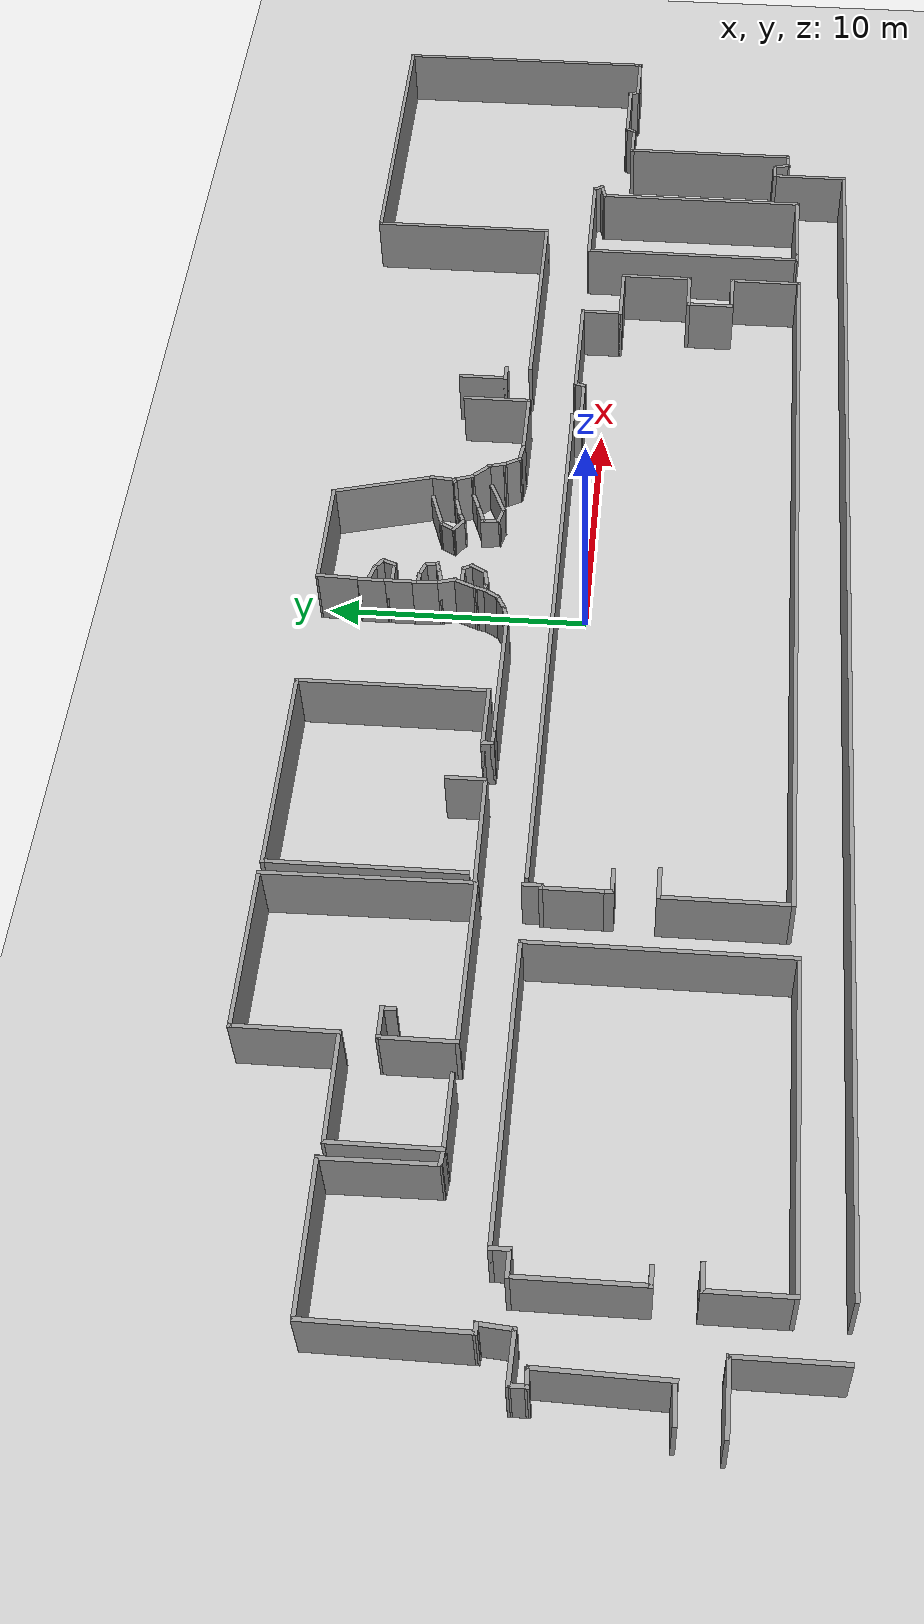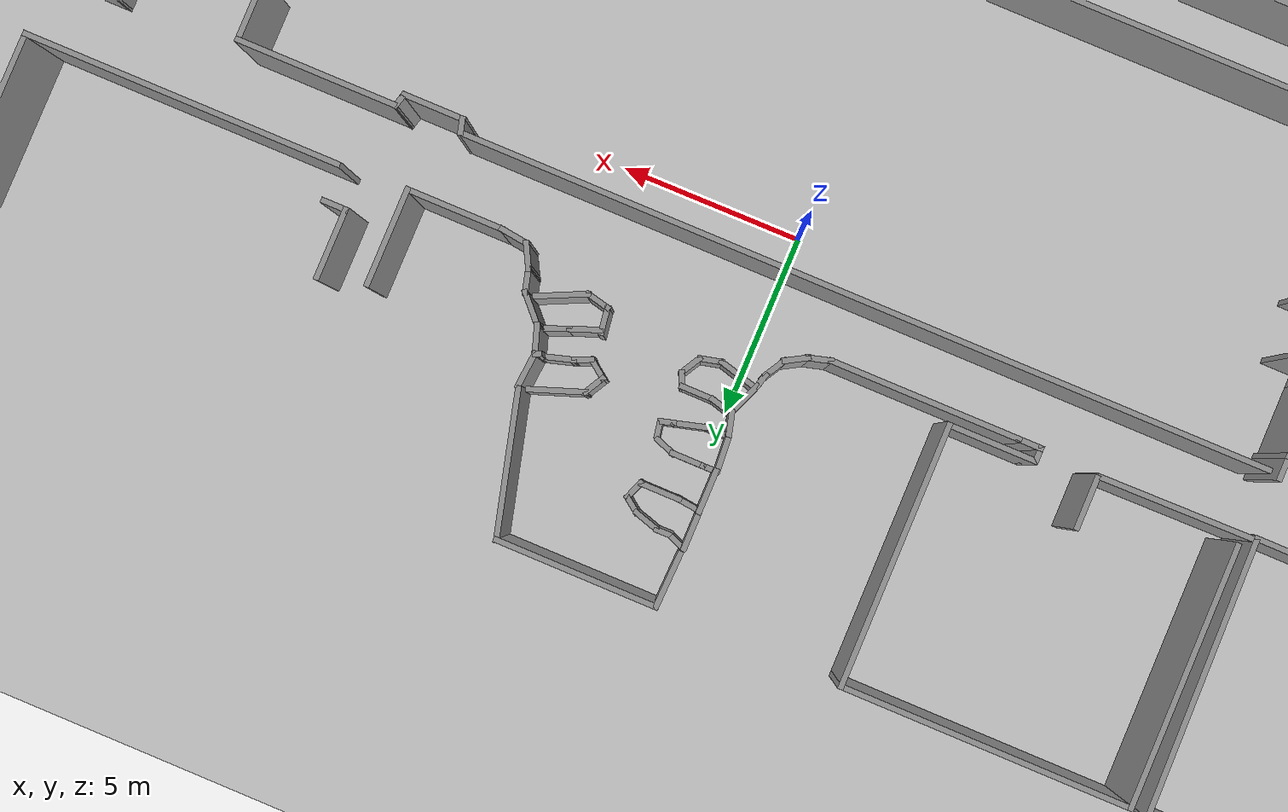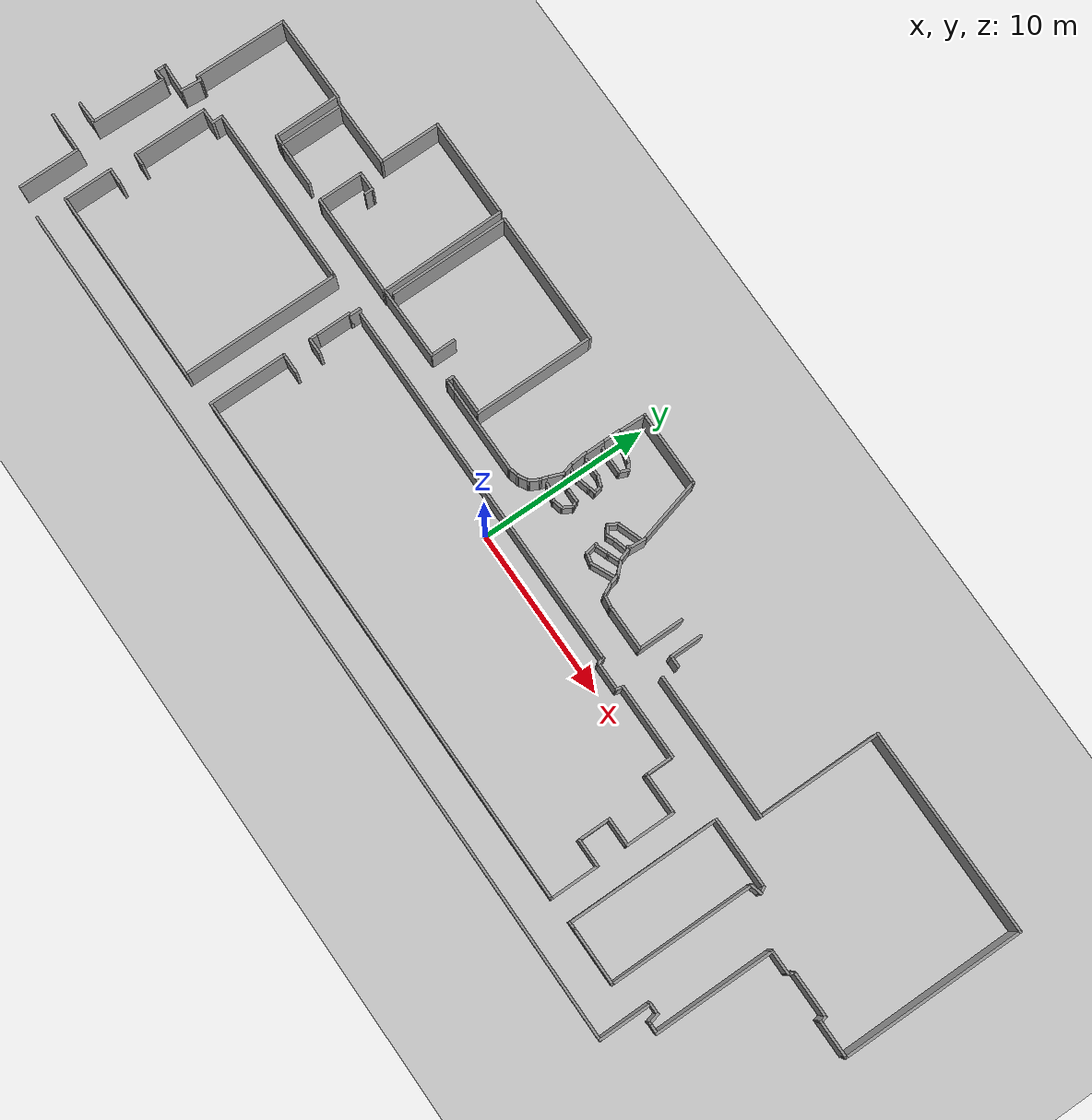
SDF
<sdf version="1.7">
 <world name="default">
  <light name="sun" type="directional">
   <pose>0 0 10 0 -0 0</pose>
   <diffuse>0.8 0.8 0.8 1</diffuse>
   <specular>0.2 0.2 0.2 1</specular>
   <attenuation>
    <range>1000</range>
    <constant>0.9</constant>
    <linear>0.01</linear>
    <quadratic>0.001</quadratic>
   </attenuation>
   <direction>-0.5 0.1 -0.9</direction>
   <spot><inner_angle>0</inner_angle><outer_angle>0</outer_angle><falloff>0</falloff></spot>
  </light>
  <model name="ground_plane">
   <static>1</static>
   <link name="link">
    <collision name="collision">
     <geometry><plane><normal>0 0 1</normal><size>100 100</size></plane></geometry>
     <surface><friction><ode><mu>100</mu><mu2>50</mu2></ode></friction></surface>
    </collision>
    <visual name="visual">
     <cast_shadows>0</cast_shadows>
     <geometry><plane><normal>0 0 1</normal><size>100 100</size></plane></geometry>
     <material>
      <script><uri>file://media/materials/scripts/gazebo.material</uri><name>Gazebo/Grey</name></script>
     </material>
    </visual>
   </link>
  </model>
  <gravity>0 0 -9.8</gravity>
  <magnetic_field>6e-06 2.3e-05 -4.2e-05</magnetic_field>
  <atmosphere type="adiabatic"/>
  <physics type="ode">
   <max_step_size>0.001</max_step_size>
   <real_time_factor>1</real_time_factor>
   <real_time_update_rate>1000</real_time_update_rate>
  </physics>
  <scene><ambient>0.4 0.4 0.4 1</ambient><background>0.7 0.7 0.7 1</background><shadows>1</shadows></scene>
  <audio><device>default</device></audio>
  <spherical_coordinates>
   <surface_model>EARTH_WGS84</surface_model>
   <latitude_deg>0</latitude_deg>
   <longitude_deg>0</longitude_deg>
   <elevation>0</elevation>
   <heading_deg>0</heading_deg>
  </spherical_coordinates>
  <model name="erzelli-sim">
   <pose>0.292126 0.213876 0 0 -0 0</pose>
   <link name="Wall_10">
    <collision name="Wall_10_Collision">
     <geometry><box><size>0.660972 0.15 2.5</size></box></geometry>
     <pose>0 0 1.25 0 -0 0</pose>
    </collision>
    <visual name="Wall_10_Visual">
     <pose>0 0 1.25 0 -0 0</pose>
     <geometry><box><size>0.660972 0.15 2.5</size></box></geometry>
     <material>
      <script><uri>file://media/materials/scripts/gazebo.material</uri><name>Gazebo/Grey</name></script>
      <ambient>1 1 1 1</ambient>
     </material>
     <meta><layer>0</layer></meta>
    </visual>
    <pose>-23.8814 2.70582 0 0 -0 3.05093</pose>
   </link>
   <link name="Wall_100">
    <collision name="Wall_100_Collision">
     <geometry><box><size>0.60562 0.15 1.5</size></box></geometry>
     <pose>0 0 0.75 0 -0 0</pose>
    </collision>
    <visual name="Wall_100_Visual">
     <pose>0 0 0.75 0 -0 0</pose>
     <geometry><box><size>0.60562 0.15 1.5</size></box></geometry>
     <material>
      <script><uri>file://media/materials/scripts/gazebo.material</uri><name>Gazebo/Grey</name></script>
      <ambient>1 1 1 1</ambient>
     </material>
     <meta><layer>0</layer></meta>
    </visual>
    <pose>3.64387 4.99562 0 0 -0 0.418447</pose>
   </link>
   <link name="Wall_101">
    <collision name="Wall_101_Collision">
     <geometry><box><size>0.969751 0.15 1.5</size></box></geometry>
     <pose>0 0 0.75 0 -0 0</pose>
    </collision>
    <visual name="Wall_101_Visual">
     <pose>0 0 0.75 0 -0 0</pose>
     <geometry><box><size>0.969751 0.15 1.5</size></box></geometry>
     <material>
      <script><uri>file://media/materials/scripts/gazebo.material</uri><name>Gazebo/Grey</name></script>
      <ambient>1 1 1 1</ambient>
     </material>
     <meta><layer>0</layer></meta>
    </visual>
    <pose>4.24537 5.20362 0 0 -0 0.285501</pose>
   </link>
   <link name="Wall_102">
    <collision name="Wall_102_Collision">
     <geometry><box><size>0.253443 0.15 2.5</size></box></geometry>
     <pose>0 0 1.25 0 -0 0</pose>
    </collision>
    <visual name="Wall_102_Visual">
     <pose>0 0 1.25 0 -0 0</pose>
     <geometry><box><size>0.253443 0.15 2.5</size></box></geometry>
     <material>
      <script><uri>file://media/materials/scripts/gazebo.material</uri><name>Gazebo/Grey</name></script>
      <ambient>1 1 1 1</ambient>
     </material>
     <meta><layer>0</layer></meta>
    </visual>
    <pose>4.68501 5.34248 0 0 -0 0.468665</pose>
   </link>
   <link name="Wall_103">
    <collision name="Wall_103_Collision">
     <geometry><box><size>0.881454 0.15 2.5</size></box></geometry>
     <pose>0 0 1.25 0 -0 0</pose>
    </collision>
    <visual name="Wall_103_Visual">
     <pose>0 0 1.25 0 -0 0</pose>
     <geometry><box><size>0.881454 0.15 2.5</size></box></geometry>
     <material>
      <script><uri>file://media/materials/scripts/gazebo.material</uri><name>Gazebo/Grey</name></script>
      <ambient>1 1 1 1</ambient>
     </material>
     <meta><layer>0</layer></meta>
    </visual>
    <pose>4.84701 5.01898 0 0 -0 -1.24842</pose>
   </link>
   <link name="Wall_104">
    <collision name="Wall_104_Collision">
     <geometry><box><size>0.89761 0.15 1.5</size></box></geometry>
     <pose>0 0 0.75 0 -0 0</pose>
    </collision>
    <visual name="Wall_104_Visual">
     <pose>0 0 0.75 0 -0 0</pose>
     <geometry><box><size>0.89761 0.15 1.5</size></box></geometry>
     <material>
      <script><uri>file://media/materials/scripts/gazebo.material</uri><name>Gazebo/Grey</name></script>
      <ambient>1 1 1 1</ambient>
     </material>
     <meta><layer>0</layer></meta>
    </visual>
    <pose>4.61587 4.53312 0 0 -0 -2.76059</pose>
   </link>
   <link name="Wall_105">
    <collision name="Wall_105_Collision">
     <geometry><box><size>0.941082 0.15 1.5</size></box></geometry>
     <pose>0 0 0.75 0 -0 0</pose>
    </collision>
    <visual name="Wall_105_Visual">
     <pose>0 0 0.75 0 -0 0</pose>
     <geometry><box><size>0.941082 0.15 1.5</size></box></geometry>
     <material>
      <script><uri>file://media/materials/scripts/gazebo.material</uri><name>Gazebo/Grey</name></script>
      <ambient>1 1 1 1</ambient>
     </material>
     <meta><layer>0</layer></meta>
    </visual>
    <pose>3.89837 4.25562 0 0 -0 -2.78386</pose>
   </link>
   <link name="Wall_107">
    <collision name="Wall_107_Collision">
     <geometry><box><size>0.804537 0.15 1.5</size></box></geometry>
     <pose>0 0 0.75 0 -0 0</pose>
    </collision>
    <visual name="Wall_107_Visual">
     <pose>0 0 0.75 0 -0 0</pose>
     <geometry><box><size>0.804537 0.15 1.5</size></box></geometry>
     <material>
      <script><uri>file://media/materials/scripts/gazebo.material</uri><name>Gazebo/Grey</name></script>
      <ambient>1 1 1 1</ambient>
     </material>
     <meta><layer>0</layer></meta>
    </visual>
    <pose>3.52837 3.83912 0 0 -0 -1.42825</pose>
   </link>
   <link name="Wall_108">
    <collision name="Wall_108_Collision">
     <geometry><box><size>0.767202 0.15 1.5</size></box></geometry>
     <pose>0 0 0.75 0 -0 0</pose>
    </collision>
    <visual name="Wall_108_Visual">
     <pose>0 0 0.75 0 -0 0</pose>
     <geometry><box><size>0.767202 0.15 1.5</size></box></geometry>
     <material>
      <script><uri>file://media/materials/scripts/gazebo.material</uri><name>Gazebo/Grey</name></script>
      <ambient>1 1 1 1</ambient>
     </material>
     <meta><layer>0</layer></meta>
    </visual>
    <pose>3.87537 3.44562 0 0 -0 -0.227285</pose>
   </link>
   <link name="Wall_109">
    <collision name="Wall_109_Collision">
     <geometry><box><size>1.68186 0.15 1.5</size></box></geometry>
     <pose>0 0 0.75 0 -0 0</pose>
    </collision>
    <visual name="Wall_109_Visual">
     <pose>0 0 0.75 0 -0 0</pose>
     <geometry><box><size>1.68186 0.15 1.5</size></box></geometry>
     <material>
      <script><uri>file://media/materials/scripts/gazebo.material</uri><name>Gazebo/Grey</name></script>
      <ambient>1 1 1 1</ambient>
     </material>
     <meta><layer>0</layer></meta>
    </visual>
    <pose>4.86987 3.70012 0 0 -0 0.436785</pose>
   </link>
   <link name="Wall_11">
    <collision name="Wall_11_Collision">
     <geometry><box><size>4.03622 0.15 2.5</size></box></geometry>
     <pose>0 0 1.25 0 -0 0</pose>
    </collision>
    <visual name="Wall_11_Visual">
     <pose>0 0 1.25 0 -0 0</pose>
     <geometry><box><size>4.03622 0.15 2.5</size></box></geometry>
     <material>
      <script><uri>file://media/materials/scripts/gazebo.material</uri><name>Gazebo/Grey</name></script>
      <ambient>1 1 1 1</ambient>
     </material>
     <meta><layer>0</layer></meta>
    </visual>
    <pose>-24.159 4.67193 0 0 -0 1.5827</pose>
   </link>
   <link name="Wall_110">
    <collision name="Wall_110_Collision">
     <geometry><box><size>0.75 0.15 2.5</size></box></geometry>
     <pose>0 0 1.25 0 -0 0</pose>
    </collision>
    <visual name="Wall_110_Visual">
     <pose>0 0 1.25 0 -0 0</pose>
     <geometry><box><size>0.75 0.15 2.5</size></box></geometry>
     <material>
      <script><uri>file://media/materials/scripts/gazebo.material</uri><name>Gazebo/Grey</name></script>
      <ambient>1 1 1 1</ambient>
     </material>
     <meta><layer>0</layer></meta>
    </visual>
    <pose>5.64151 3.73442 0 0 -0 -1.30896</pose>
   </link>
   <link name="Wall_111">
    <collision name="Wall_111_Collision">
     <geometry><box><size>0.803717 0.15 2.5</size></box></geometry>
     <pose>0 0 1.25 0 -0 0</pose>
    </collision>
    <visual name="Wall_111_Visual">
     <pose>0 0 1.25 0 -0 0</pose>
     <geometry><box><size>0.803717 0.15 2.5</size></box></geometry>
     <material>
      <script><uri>file://media/materials/scripts/gazebo.material</uri><name>Gazebo/Grey</name></script>
      <ambient>1 1 1 1</ambient>
     </material>
     <meta><layer>0</layer></meta>
    </visual>
    <pose>5.87281 3.15623 0 0 -0 -1.08138</pose>
   </link>
   <link name="Wall_112">
    <collision name="Wall_112_Collision">
     <geometry><box><size>0.850059 0.15 2.5</size></box></geometry>
     <pose>0 0 1.25 0 -0 0</pose>
    </collision>
    <visual name="Wall_112_Visual">
     <pose>0 0 1.25 0 -0 0</pose>
     <geometry><box><size>0.850059 0.15 2.5</size></box></geometry>
     <material>
      <script><uri>file://media/materials/scripts/gazebo.material</uri><name>Gazebo/Grey</name></script>
      <ambient>1 1 1 1</ambient>
     </material>
     <meta><layer>0</layer></meta>
    </visual>
    <pose>6.37343 2.82148 0 0 -0 -0.132552</pose>
   </link>
   <link name="Wall_113">
    <collision name="Wall_113_Collision">
     <geometry><box><size>2.75 0.15 2.5</size></box></geometry>
     <pose>0 0 1.25 0 -0 0</pose>
    </collision>
    <visual name="Wall_113_Visual">
     <pose>0 0 1.25 0 -0 0</pose>
     <geometry><box><size>2.75 0.15 2.5</size></box></geometry>
     <material>
      <script><uri>file://media/materials/scripts/gazebo.material</uri><name>Gazebo/Grey</name></script>
      <ambient>1 1 1 1</ambient>
     </material>
     <meta><layer>0</layer></meta>
    </visual>
    <pose>8.02039 2.77522 0 0 -0 0</pose>
   </link>
   <link name="Wall_114">
    <collision name="Wall_114_Collision">
     <geometry><box><size>2.75 0.15 2.5</size></box></geometry>
     <pose>0 0 1.25 0 -0 0</pose>
    </collision>
    <visual name="Wall_114_Visual">
     <pose>0 0 1.25 0 -0 0</pose>
     <geometry><box><size>2.75 0.15 2.5</size></box></geometry>
     <material>
      <script><uri>file://media/materials/scripts/gazebo.material</uri><name>Gazebo/Grey</name></script>
      <ambient>1 1 1 1</ambient>
     </material>
     <meta><layer>0</layer></meta>
    </visual>
    <pose>9.32039 4.07522 0 0 -0 1.5708</pose>
   </link>
   <link name="Wall_117">
    <collision name="Wall_117_Collision">
     <geometry><box><size>8.75 0.15 2.5</size></box></geometry>
     <pose>0 0 1.25 0 -0 0</pose>
    </collision>
    <visual name="Wall_117_Visual">
     <pose>0 0 1.25 0 -0 0</pose>
     <geometry><box><size>8.75 0.15 2.5</size></box></geometry>
     <material>
      <script><uri>file://media/materials/scripts/gazebo.material</uri><name>Gazebo/Grey</name></script>
      <ambient>1 1 1 1</ambient>
     </material>
     <meta><layer>0</layer></meta>
    </visual>
    <pose>15.5077 2.86774 0 0 -0 0</pose>
   </link>
   <link name="Wall_118">
    <collision name="Wall_118_Collision">
     <geometry><box><size>7.5 0.15 2.5</size></box></geometry>
     <pose>0 0 1.25 0 -0 0</pose>
    </collision>
    <visual name="Wall_118_Visual">
     <pose>0 0 1.25 0 -0 0</pose>
     <geometry><box><size>7.5 0.15 2.5</size></box></geometry>
     <material>
      <script><uri>file://media/materials/scripts/gazebo.material</uri><name>Gazebo/Grey</name></script>
      <ambient>1 1 1 1</ambient>
     </material>
     <meta><layer>0</layer></meta>
    </visual>
    <pose>19.8077 6.54274 0 0 -0 1.5708</pose>
   </link>
   <link name="Wall_119">
    <collision name="Wall_119_Collision">
     <geometry><box><size>12.25 0.15 2.5</size></box></geometry>
     <pose>0 0 1.25 0 -0 0</pose>
    </collision>
    <visual name="Wall_119_Visual">
     <pose>0 0 1.25 0 -0 0</pose>
     <geometry><box><size>12.25 0.15 2.5</size></box></geometry>
     <material>
      <script><uri>file://media/materials/scripts/gazebo.material</uri><name>Gazebo/Grey</name></script>
      <ambient>1 1 1 1</ambient>
     </material>
     <meta><layer>0</layer></meta>
    </visual>
    <pose>25.8577 10.2177 0 0 -0 0</pose>
   </link>
   <link name="Wall_12">
    <collision name="Wall_12_Collision">
     <geometry><box><size>5.2852 0.15 2.5</size></box></geometry>
     <pose>0 0 1.25 0 -0 0</pose>
    </collision>
    <visual name="Wall_12_Visual">
     <pose>0 0 1.25 0 -0 0</pose>
     <geometry><box><size>5.2852 0.15 2.5</size></box></geometry>
     <material>
      <script><uri>file://media/materials/scripts/gazebo.material</uri><name>Gazebo/Grey</name></script>
      <ambient>1 1 1 1</ambient>
     </material>
     <meta><layer>0</layer></meta>
    </visual>
    <pose>-26.7033 6.59177 0 0 -0 -3.13258</pose>
   </link>
   <link name="Wall_120">
    <collision name="Wall_120_Collision">
     <geometry><box><size>11 0.15 2.5</size></box></geometry>
     <pose>0 0 1.25 0 -0 0</pose>
    </collision>
    <visual name="Wall_120_Visual">
     <pose>0 0 1.25 0 -0 0</pose>
     <geometry><box><size>11 0.15 2.5</size></box></geometry>
     <material>
      <script><uri>file://media/materials/scripts/gazebo.material</uri><name>Gazebo/Grey</name></script>
      <ambient>1 1 1 1</ambient>
     </material>
     <meta><layer>0</layer></meta>
    </visual>
    <pose>31.9077 4.79274 0 0 -0 -1.5708</pose>
   </link>
   <link name="Wall_121">
    <collision name="Wall_121_Collision">
     <geometry><box><size>2.25 0.15 2.5</size></box></geometry>
     <pose>0 0 1.25 0 -0 0</pose>
    </collision>
    <visual name="Wall_121_Visual">
     <pose>0 0 1.25 0 -0 0</pose>
     <geometry><box><size>2.25 0.15 2.5</size></box></geometry>
     <material>
      <script><uri>file://media/materials/scripts/gazebo.material</uri><name>Gazebo/Grey</name></script>
      <ambient>1 1 1 1</ambient>
     </material>
     <meta><layer>0</layer></meta>
    </visual>
    <pose>30.8577 -0.632261 0 0 -0 3.14159</pose>
   </link>
   <link name="Wall_122">
    <collision name="Wall_122_Collision">
     <geometry><box><size>0.5 0.15 2.5</size></box></geometry>
     <pose>0 0 1.25 0 -0 0</pose>
    </collision>
    <visual name="Wall_122_Visual">
     <pose>0 0 1.25 0 -0 0</pose>
     <geometry><box><size>0.5 0.15 2.5</size></box></geometry>
     <material>
      <script><uri>file://media/materials/scripts/gazebo.material</uri><name>Gazebo/Grey</name></script>
      <ambient>1 1 1 1</ambient>
     </material>
     <meta><layer>0</layer></meta>
    </visual>
    <pose>29.7624 -0.463224 0 0 -0 1.8326</pose>
   </link>
   <link name="Wall_123">
    <collision name="Wall_123_Collision">
     <geometry><box><size>2.75 0.15 2.5</size></box></geometry>
     <pose>0 0 1.25 0 -0 0</pose>
    </collision>
    <visual name="Wall_123_Visual">
     <pose>0 0 1.25 0 -0 0</pose>
     <geometry><box><size>2.75 0.15 2.5</size></box></geometry>
     <material>
      <script><uri>file://media/materials/scripts/gazebo.material</uri><name>Gazebo/Grey</name></script>
      <ambient>1 1 1 1</ambient>
     </material>
     <meta><layer>0</layer></meta>
    </visual>
    <pose>28.4171 -0.294187 0 0 -0 3.14159</pose>
   </link>
   <link name="Wall_124">
    <collision name="Wall_124_Collision">
     <geometry><box><size>0.5 0.15 2.5</size></box></geometry>
     <pose>0 0 1.25 0 -0 0</pose>
    </collision>
    <visual name="Wall_124_Visual">
     <pose>0 0 1.25 0 -0 0</pose>
     <geometry><box><size>0.5 0.15 2.5</size></box></geometry>
     <material>
      <script><uri>file://media/materials/scripts/gazebo.material</uri><name>Gazebo/Grey</name></script>
      <ambient>1 1 1 1</ambient>
     </material>
     <meta><layer>0</layer></meta>
    </visual>
    <pose>27.0296 -0.445741 0 0 -0 -2.0944</pose>
   </link>
   <link name="Wall_125">
    <collision name="Wall_125_Collision">
     <geometry><box><size>1.5 0.15 2.5</size></box></geometry>
     <pose>0 0 1.25 0 -0 0</pose>
    </collision>
    <visual name="Wall_125_Visual">
     <pose>0 0 1.25 0 -0 0</pose>
     <geometry><box><size>1.5 0.15 2.5</size></box></geometry>
     <material>
      <script><uri>file://media/materials/scripts/gazebo.material</uri><name>Gazebo/Grey</name></script>
      <ambient>1 1 1 1</ambient>
     </material>
     <meta><layer>0</layer></meta>
    </visual>
    <pose>26.2671 -0.597296 0 0 -0 3.14159</pose>
   </link>
   <link name="Wall_126">
    <collision name="Wall_126_Collision">
     <geometry><box><size>7.25 0.15 2.5</size></box></geometry>
     <pose>0 0 1.25 0 -0 0</pose>
    </collision>
    <visual name="Wall_126_Visual">
     <pose>0 0 1.25 0 -0 0</pose>
     <geometry><box><size>7.25 0.15 2.5</size></box></geometry>
     <material>
      <script><uri>file://media/materials/scripts/gazebo.material</uri><name>Gazebo/Grey</name></script>
      <ambient>1 1 1 1</ambient>
     </material>
     <meta><layer>0</layer></meta>
    </visual>
    <pose>25.5921 -4.14729 0 0 -0 -1.5708</pose>
   </link>
   <link name="Wall_127">
    <collision name="Wall_127_Collision">
     <geometry><box><size>0.75 0.15 2.5</size></box></geometry>
     <pose>0 0 1.25 0 -0 0</pose>
    </collision>
    <visual name="Wall_127_Visual">
     <pose>0 0 1.25 0 -0 0</pose>
     <geometry><box><size>0.75 0.15 2.5</size></box></geometry>
     <material>
      <script><uri>file://media/materials/scripts/gazebo.material</uri><name>Gazebo/Grey</name></script>
      <ambient>1 1 1 1</ambient>
     </material>
     <meta><layer>0</layer></meta>
    </visual>
    <pose>25.2921 -7.6973 0 0 -0 3.14159</pose>
   </link>
   <link name="Wall_128">
    <collision name="Wall_128_Collision">
     <geometry><box><size>0.75 0.15 2.5</size></box></geometry>
     <pose>0 0 1.25 0 -0 0</pose>
    </collision>
    <visual name="Wall_128_Visual">
     <pose>0 0 1.25 0 -0 0</pose>
     <geometry><box><size>0.75 0.15 2.5</size></box></geometry>
     <material>
      <script><uri>file://media/materials/scripts/gazebo.material</uri><name>Gazebo/Grey</name></script>
      <ambient>1 1 1 1</ambient>
     </material>
     <meta><layer>0</layer></meta>
    </visual>
    <pose>24.9145 -7.40752 0 0 -0 1.8326</pose>
   </link>
   <link name="Wall_129">
    <collision name="Wall_129_Collision">
     <geometry><box><size>0.75 0.15 2.5</size></box></geometry>
     <pose>0 0 1.25 0 -0 0</pose>
    </collision>
    <visual name="Wall_129_Visual">
     <pose>0 0 1.25 0 -0 0</pose>
     <geometry><box><size>0.75 0.15 2.5</size></box></geometry>
     <material>
      <script><uri>file://media/materials/scripts/gazebo.material</uri><name>Gazebo/Grey</name></script>
      <ambient>1 1 1 1</ambient>
     </material>
     <meta><layer>0</layer></meta>
    </visual>
    <pose>24.5368 -7.11774 0 0 -0 3.14159</pose>
   </link>
   <link name="Wall_13">
    <collision name="Wall_13_Collision">
     <geometry><box><size>5.60902 0.15 2.5</size></box></geometry>
     <pose>0 0 1.25 0 -0 0</pose>
    </collision>
    <visual name="Wall_13_Visual">
     <pose>0 0 1.25 0 -0 0</pose>
     <geometry><box><size>5.60902 0.15 2.5</size></box></geometry>
     <material>
      <script><uri>file://media/materials/scripts/gazebo.material</uri><name>Gazebo/Grey</name></script>
      <ambient>1 1 1 1</ambient>
     </material>
     <meta><layer>0</layer></meta>
    </visual>
    <pose>-29.3402 3.83922 0 0 -0 -1.57927</pose>
   </link>
   <link name="Wall_130">
    <collision name="Wall_130_Collision">
     <geometry><box><size>3.25 0.15 2.5</size></box></geometry>
     <pose>0 0 1.25 0 -0 0</pose>
    </collision>
    <visual name="Wall_130_Visual">
     <pose>0 0 1.25 0 -0 0</pose>
     <geometry><box><size>3.25 0.15 2.5</size></box></geometry>
     <material>
      <script><uri>file://media/materials/scripts/gazebo.material</uri><name>Gazebo/Grey</name></script>
      <ambient>1 1 1 1</ambient>
     </material>
     <meta><layer>0</layer></meta>
    </visual>
    <pose>24.2368 -8.66774 0 0 -0 -1.5708</pose>
   </link>
   <link name="Wall_131">
    <collision name="Wall_131_Collision">
     <geometry><box><size>52 0.15 2.5</size></box></geometry>
     <pose>0 0 1.25 0 -0 0</pose>
    </collision>
    <visual name="Wall_131_Visual">
     <pose>0 0 1.25 0 -0 0</pose>
     <geometry><box><size>52 0.15 2.5</size></box></geometry>
     <material>
      <script><uri>file://media/materials/scripts/gazebo.material</uri><name>Gazebo/Grey</name></script>
      <ambient>1 1 1 1</ambient>
     </material>
     <meta><layer>0</layer></meta>
    </visual>
    <pose>-1.68815 -10.2177 0 0 -0 3.14159</pose>
   </link>
   <link name="Wall_135">
    <collision name="Wall_135_Collision">
     <geometry><box><size>4.25 0.15 2.5</size></box></geometry>
     <pose>0 0 1.25 0 -0 0</pose>
    </collision>
    <visual name="Wall_135_Visual">
     <pose>0 0 1.25 0 -0 0</pose>
     <geometry><box><size>4.25 0.15 2.5</size></box></geometry>
     <material>
      <script><uri>file://media/materials/scripts/gazebo.material</uri><name>Gazebo/Grey</name></script>
      <ambient>1 1 1 1</ambient>
     </material>
     <meta><layer>0</layer></meta>
    </visual>
    <pose>20.7058 0.924768 0 0 -0 0</pose>
   </link>
   <link name="Wall_136">
    <collision name="Wall_136_Collision">
     <geometry><box><size>0.5 0.15 2.5</size></box></geometry>
     <pose>0 0 1.25 0 -0 0</pose>
    </collision>
    <visual name="Wall_136_Visual">
     <pose>0 0 1.25 0 -0 0</pose>
     <geometry><box><size>0.5 0.15 2.5</size></box></geometry>
     <material>
      <script><uri>file://media/materials/scripts/gazebo.material</uri><name>Gazebo/Grey</name></script>
      <ambient>1 1 1 1</ambient>
     </material>
     <meta><layer>0</layer></meta>
    </visual>
    <pose>22.8433 0.773214 0 0 -0 -1.0472</pose>
   </link>
   <link name="Wall_137">
    <collision name="Wall_137_Collision">
     <geometry><box><size>0.75 0.15 2.5</size></box></geometry>
     <pose>0 0 1.25 0 -0 0</pose>
    </collision>
    <visual name="Wall_137_Visual">
     <pose>0 0 1.25 0 -0 0</pose>
     <geometry><box><size>0.75 0.15 2.5</size></box></geometry>
     <material>
      <script><uri>file://media/materials/scripts/gazebo.material</uri><name>Gazebo/Grey</name></script>
      <ambient>1 1 1 1</ambient>
     </material>
     <meta><layer>0</layer></meta>
    </visual>
    <pose>22.641 0.544014 0 0 -0 -2.87979</pose>
   </link>
   <link name="Wall_138">
    <collision name="Wall_138_Collision">
     <geometry><box><size>8.75 0.15 2.5</size></box></geometry>
     <pose>0 0 1.25 0 -0 0</pose>
    </collision>
    <visual name="Wall_138_Visual">
     <pose>0 0 1.25 0 -0 0</pose>
     <geometry><box><size>8.75 0.15 2.5</size></box></geometry>
     <material>
      <script><uri>file://media/materials/scripts/gazebo.material</uri><name>Gazebo/Grey</name></script>
      <ambient>1 1 1 1</ambient>
     </material>
     <meta><layer>0</layer></meta>
    </visual>
    <pose>22.3512 -3.83363 0 0 -0 -1.5708</pose>
   </link>
   <link name="Wall_139">
    <collision name="Wall_139_Collision">
     <geometry><box><size>3.5 0.15 2.5</size></box></geometry>
     <pose>0 0 1.25 0 -0 0</pose>
    </collision>
    <visual name="Wall_139_Visual">
     <pose>0 0 1.25 0 -0 0</pose>
     <geometry><box><size>3.5 0.15 2.5</size></box></geometry>
     <material>
      <script><uri>file://media/materials/scripts/gazebo.material</uri><name>Gazebo/Grey</name></script>
      <ambient>1 1 1 1</ambient>
     </material>
     <meta><layer>0</layer></meta>
    </visual>
    <pose>20.6762 -8.13363 0 0 -0 3.14159</pose>
   </link>
   <link name="Wall_14">
    <collision name="Wall_14_Collision">
     <geometry><box><size>0.427567 0.15 2.5</size></box></geometry>
     <pose>0 0 1.25 0 -0 0</pose>
    </collision>
    <visual name="Wall_14_Visual">
     <pose>0 0 1.25 0 -0 0</pose>
     <geometry><box><size>0.427567 0.15 2.5</size></box></geometry>
     <material>
      <script><uri>file://media/materials/scripts/gazebo.material</uri><name>Gazebo/Grey</name></script>
      <ambient>1 1 1 1</ambient>
     </material>
     <meta><layer>0</layer></meta>
    </visual>
    <pose>-29.2246 1.10981 0 0 -0 0</pose>
   </link>
   <link name="Wall_140">
    <collision name="Wall_140_Collision">
     <geometry><box><size>0.5 0.15 2.5</size></box></geometry>
     <pose>0 0 1.25 0 -0 0</pose>
    </collision>
    <visual name="Wall_140_Visual">
     <pose>0 0 1.25 0 -0 0</pose>
     <geometry><box><size>0.5 0.15 2.5</size></box></geometry>
     <material>
      <script><uri>file://media/materials/scripts/gazebo.material</uri><name>Gazebo/Grey</name></script>
      <ambient>1 1 1 1</ambient>
     </material>
     <meta><layer>0</layer></meta>
    </visual>
    <pose>18.8262 -8.13363 0 0 -0 3.14159</pose>
   </link>
   <link name="Wall_141">
    <collision name="Wall_141_Collision">
     <geometry><box><size>9.2084 0.15 2.5</size></box></geometry>
     <pose>0 0 1.25 0 -0 0</pose>
    </collision>
    <visual name="Wall_141_Visual">
     <pose>0 0 1.25 0 -0 0</pose>
     <geometry><box><size>9.2084 0.15 2.5</size></box></geometry>
     <material>
      <script><uri>file://media/materials/scripts/gazebo.material</uri><name>Gazebo/Grey</name></script>
      <ambient>1 1 1 1</ambient>
     </material>
     <meta><layer>0</layer></meta>
    </visual>
    <pose>18.6535 -3.60443 0 0 -0 1.57029</pose>
   </link>
   <link name="Wall_143">
    <collision name="Wall_143_Collision">
     <geometry><box><size>0.75 0.15 2.5</size></box></geometry>
     <pose>0 0 1.25 0 -0 0</pose>
    </collision>
    <visual name="Wall_143_Visual">
     <pose>0 0 1.25 0 -0 0</pose>
     <geometry><box><size>0.75 0.15 2.5</size></box></geometry>
     <material>
      <script><uri>file://media/materials/scripts/gazebo.material</uri><name>Gazebo/Grey</name></script>
      <ambient>1 1 1 1</ambient>
     </material>
     <meta><layer>0</layer></meta>
    </visual>
    <pose>-7.64302 2.63643 0 0 -0 3.14159</pose>
   </link>
   <link name="Wall_144">
    <collision name="Wall_144_Collision">
     <geometry><box><size>0.5 0.15 2.5</size></box></geometry>
     <pose>0 0 1.25 0 -0 0</pose>
    </collision>
    <visual name="Wall_144_Visual">
     <pose>0 0 1.25 0 -0 0</pose>
     <geometry><box><size>0.5 0.15 2.5</size></box></geometry>
     <material>
      <script><uri>file://media/materials/scripts/gazebo.material</uri><name>Gazebo/Grey</name></script>
      <ambient>1 1 1 1</ambient>
     </material>
     <meta><layer>0</layer></meta>
    </visual>
    <pose>-7.94302 2.81143 0 0 -0 1.5708</pose>
   </link>
   <link name="Wall_145">
    <collision name="Wall_145_Collision">
     <geometry><box><size>2.5 0.15 2.5</size></box></geometry>
     <pose>0 0 1.25 0 -0 0</pose>
    </collision>
    <visual name="Wall_145_Visual">
     <pose>0 0 1.25 0 -0 0</pose>
     <geometry><box><size>2.5 0.15 2.5</size></box></geometry>
     <material>
      <script><uri>file://media/materials/scripts/gazebo.material</uri><name>Gazebo/Grey</name></script>
      <ambient>1 1 1 1</ambient>
     </material>
     <meta><layer>0</layer></meta>
    </visual>
    <pose>-6.76802 2.98643 0 0 -0 0</pose>
   </link>
   <link name="Wall_146">
    <collision name="Wall_146_Collision">
     <geometry><box><size>7.25 0.15 2.5</size></box></geometry>
     <pose>0 0 1.25 0 -0 0</pose>
    </collision>
    <visual name="Wall_146_Visual">
     <pose>0 0 1.25 0 -0 0</pose>
     <geometry><box><size>7.25 0.15 2.5</size></box></geometry>
     <material>
      <script><uri>file://media/materials/scripts/gazebo.material</uri><name>Gazebo/Grey</name></script>
      <ambient>1 1 1 1</ambient>
     </material>
     <meta><layer>0</layer></meta>
    </visual>
    <pose>-5.59302 6.53643 0 0 -0 1.5708</pose>
   </link>
   <link name="Wall_147">
    <collision name="Wall_147_Collision">
     <geometry><box><size>8 0.15 2.5</size></box></geometry>
     <pose>0 0 1.25 0 -0 0</pose>
    </collision>
    <visual name="Wall_147_Visual">
     <pose>0 0 1.25 0 -0 0</pose>
     <geometry><box><size>8 0.15 2.5</size></box></geometry>
     <material>
      <script><uri>file://media/materials/scripts/gazebo.material</uri><name>Gazebo/Grey</name></script>
      <ambient>1 1 1 1</ambient>
     </material>
     <meta><layer>0</layer></meta>
    </visual>
    <pose>-9.51802 10.0864 0 0 -0 3.14159</pose>
   </link>
   <link name="Wall_148">
    <collision name="Wall_148_Collision">
     <geometry><box><size>7.25 0.15 2.5</size></box></geometry>
     <pose>0 0 1.25 0 -0 0</pose>
    </collision>
    <visual name="Wall_148_Visual">
     <pose>0 0 1.25 0 -0 0</pose>
     <geometry><box><size>7.25 0.15 2.5</size></box></geometry>
     <material>
      <script><uri>file://media/materials/scripts/gazebo.material</uri><name>Gazebo/Grey</name></script>
      <ambient>1 1 1 1</ambient>
     </material>
     <meta><layer>0</layer></meta>
    </visual>
    <pose>-13.443 6.53643 0 0 -0 -1.5708</pose>
   </link>
   <link name="Wall_15">
    <collision name="Wall_15_Collision">
     <geometry><box><size>1.31022 0.15 2.5</size></box></geometry>
     <pose>0 0 1.25 0 -0 0</pose>
    </collision>
    <visual name="Wall_15_Visual">
     <pose>0 0 1.25 0 -0 0</pose>
     <geometry><box><size>1.31022 0.15 2.5</size></box></geometry>
     <material>
      <script><uri>file://media/materials/scripts/gazebo.material</uri><name>Gazebo/Grey</name></script>
      <ambient>1 1 1 1</ambient>
     </material>
     <meta><layer>0</layer></meta>
    </visual>
    <pose>-29.1321 0.531548 0 0 -0 -1.65063</pose>
   </link>
   <link name="Wall_151">
    <collision name="Wall_151_Collision">
     <geometry><box><size>2.75 0.15 2.5</size></box></geometry>
     <pose>0 0 1.25 0 -0 0</pose>
    </collision>
    <visual name="Wall_151_Visual">
     <pose>0 0 1.25 0 -0 0</pose>
     <geometry><box><size>2.75 0.15 2.5</size></box></geometry>
     <material>
      <script><uri>file://media/materials/scripts/gazebo.material</uri><name>Gazebo/Grey</name></script>
      <ambient>1 1 1 1</ambient>
     </material>
     <meta><layer>0</layer></meta>
    </visual>
    <pose>-19.8798 3.93643 0 0 -0 1.5708</pose>
   </link>
   <link name="Wall_152">
    <collision name="Wall_152_Collision">
     <geometry><box><size>1.21072 0.15 2.5</size></box></geometry>
     <pose>0 0 1.25 0 -0 0</pose>
    </collision>
    <visual name="Wall_152_Visual">
     <pose>0 0 1.25 0 -0 0</pose>
     <geometry><box><size>1.21072 0.15 2.5</size></box></geometry>
     <material>
      <script><uri>file://media/materials/scripts/gazebo.material</uri><name>Gazebo/Grey</name></script>
      <ambient>1 1 1 1</ambient>
     </material>
     <meta><layer>0</layer></meta>
    </visual>
    <pose>-19.3495 5.23939 0 0 -0 0.005568</pose>
   </link>
   <link name="Wall_153">
    <collision name="Wall_153_Collision">
     <geometry><box><size>0.552664 0.15 2.5</size></box></geometry>
     <pose>0 0 1.25 0 -0 0</pose>
    </collision>
    <visual name="Wall_153_Visual">
     <pose>0 0 1.25 0 -0 0</pose>
     <geometry><box><size>0.552664 0.15 2.5</size></box></geometry>
     <material>
      <script><uri>file://media/materials/scripts/gazebo.material</uri><name>Gazebo/Grey</name></script>
      <ambient>1 1 1 1</ambient>
     </material>
     <meta><layer>0</layer></meta>
    </visual>
    <pose>-18.8191 5.04109 0 0 -0 -1.5708</pose>
   </link>
   <link name="Wall_155">
    <collision name="Wall_155_Collision">
     <geometry><box><size>1.06344 0.15 2.5</size></box></geometry>
     <pose>0 0 1.25 0 -0 0</pose>
    </collision>
    <visual name="Wall_155_Visual">
     <pose>0 0 1.25 0 -0 0</pose>
     <geometry><box><size>1.06344 0.15 2.5</size></box></geometry>
     <material>
      <script><uri>file://media/materials/scripts/gazebo.material</uri><name>Gazebo/Grey</name></script>
      <ambient>1 1 1 1</ambient>
     </material>
     <meta><layer>0</layer></meta>
    </visual>
    <pose>-0.584626 4.37362 0 0 -0 -1.94866</pose>
   </link>
   <link name="Wall_157">
    <collision name="Wall_157_Collision">
     <geometry><box><size>1.0338 0.15 2.5</size></box></geometry>
     <pose>0 0 1.25 0 -0 0</pose>
    </collision>
    <visual name="Wall_157_Visual">
     <pose>0 0 1.25 0 -0 0</pose>
     <geometry><box><size>1.0338 0.15 2.5</size></box></geometry>
     <material>
      <script><uri>file://media/materials/scripts/gazebo.material</uri><name>Gazebo/Grey</name></script>
      <ambient>1 1 1 1</ambient>
     </material>
     <meta><layer>0</layer></meta>
    </visual>
    <pose>5.26337 4.34812 0 0 -0 -0.823011</pose>
   </link>
   <link name="Wall_159">
    <collision name="Wall_159_Collision">
     <geometry><box><size>1.05499 0.15 2.5</size></box></geometry>
     <pose>0 0 1.25 0 -0 0</pose>
    </collision>
    <visual name="Wall_159_Visual">
     <pose>0 0 1.25 0 -0 0</pose>
     <geometry><box><size>1.05499 0.15 2.5</size></box></geometry>
     <material>
      <script><uri>file://media/materials/scripts/gazebo.material</uri><name>Gazebo/Grey</name></script>
      <ambient>1 1 1 1</ambient>
     </material>
     <meta><layer>0</layer></meta>
    </visual>
    <pose>4.77026 5.81665 0 0 -0 1.48427</pose>
   </link>
   <link name="Wall_16">
    <collision name="Wall_16_Collision">
     <geometry><box><size>1.8154 0.15 2.5</size></box></geometry>
     <pose>0 0 1.25 0 -0 0</pose>
    </collision>
    <visual name="Wall_16_Visual">
     <pose>0 0 1.25 0 -0 0</pose>
     <geometry><box><size>1.8154 0.15 2.5</size></box></geometry>
     <material>
      <script><uri>file://media/materials/scripts/gazebo.material</uri><name>Gazebo/Grey</name></script>
      <ambient>1 1 1 1</ambient>
     </material>
     <meta><layer>0</layer></meta>
    </visual>
    <pose>-30.011 -0.023587 0 0 -0 3.11382</pose>
   </link>
   <link name="Wall_162">
    <collision name="Wall_162_Collision">
     <geometry><box><size>0.668222 0.15 1.5</size></box></geometry>
     <pose>0 0 0.75 0 -0 0</pose>
    </collision>
    <visual name="Wall_162_Visual">
     <pose>0 0 0.75 0 -0 0</pose>
     <geometry><box><size>0.668222 0.15 1.5</size></box></geometry>
     <material>
      <script><uri>file://media/materials/scripts/gazebo.material</uri><name>Gazebo/Grey</name></script>
      <ambient>1 1 1 1</ambient>
     </material>
     <meta><layer>0</layer></meta>
    </visual>
    <pose>0.821374 6.23812 0 0 -0 -0.346791</pose>
   </link>
   <link name="Wall_164">
    <collision name="Wall_164_Collision">
     <geometry><box><size>0.999182 0.15 2.5</size></box></geometry>
     <pose>0 0 1.25 0 -0 0</pose>
    </collision>
    <visual name="Wall_164_Visual">
     <pose>0 0 1.25 0 -0 0</pose>
     <geometry><box><size>0.999182 0.15 2.5</size></box></geometry>
     <material>
      <script><uri>file://media/materials/scripts/gazebo.material</uri><name>Gazebo/Grey</name></script>
      <ambient>1 1 1 1</ambient>
     </material>
     <meta><layer>0</layer></meta>
    </visual>
    <pose>-0.620502 5.91395 0 0 -0 -1.49311</pose>
   </link>
   <link name="Wall_166">
    <collision name="Wall_166_Collision">
     <geometry><box><size>1.05062 0.15 2.5</size></box></geometry>
     <pose>0 0 1.25 0 -0 0</pose>
    </collision>
    <visual name="Wall_166_Visual">
     <pose>0 0 1.25 0 -0 0</pose>
     <geometry><box><size>1.05062 0.15 2.5</size></box></geometry>
     <material>
      <script><uri>file://media/materials/scripts/gazebo.material</uri><name>Gazebo/Grey</name></script>
      <ambient>1 1 1 1</ambient>
     </material>
     <meta><layer>0</layer></meta>
    </visual>
    <pose>-0.627738 7.981 0 0 -0 -1.5708</pose>
   </link>
   <link name="Wall_168">
    <collision name="Wall_168_Collision">
     <geometry><box><size>2 0.15 2.5</size></box></geometry>
     <pose>0 0 1.25 0 -0 0</pose>
    </collision>
    <visual name="Wall_168_Visual">
     <pose>0 0 1.25 0 -0 0</pose>
     <geometry><box><size>2 0.15 2.5</size></box></geometry>
     <material>
      <script><uri>file://media/materials/scripts/gazebo.material</uri><name>Gazebo/Grey</name></script>
      <ambient>1 1 1 1</ambient>
     </material>
     <meta><layer>0</layer></meta>
    </visual>
    <pose>10.5623 4.77949 0 0 -0 -1.5708</pose>
   </link>
   <link name="Wall_169">
    <collision name="Wall_169_Collision">
     <geometry><box><size>0.75 0.15 2.5</size></box></geometry>
     <pose>0 0 1.25 0 -0 0</pose>
    </collision>
    <visual name="Wall_169_Visual">
     <pose>0 0 1.25 0 -0 0</pose>
     <geometry><box><size>0.75 0.15 2.5</size></box></geometry>
     <material>
      <script><uri>file://media/materials/scripts/gazebo.material</uri><name>Gazebo/Grey</name></script>
      <ambient>1 1 1 1</ambient>
     </material>
     <meta><layer>0</layer></meta>
    </visual>
    <pose>10.8623 3.85449 0 0 -0 0</pose>
   </link>
   <link name="Wall_17">
    <collision name="Wall_17_Collision">
     <geometry><box><size>0.705135 0.15 2.5</size></box></geometry>
     <pose>0 0 1.25 0 -0 0</pose>
    </collision>
    <visual name="Wall_17_Visual">
     <pose>0 0 1.25 0 -0 0</pose>
     <geometry><box><size>0.705135 0.15 2.5</size></box></geometry>
     <material>
      <script><uri>file://media/materials/scripts/gazebo.material</uri><name>Gazebo/Grey</name></script>
      <ambient>1 1 1 1</ambient>
     </material>
     <meta><layer>0</layer></meta>
    </visual>
    <pose>-30.8437 -0.278023 0 0 -0 -1.5708</pose>
   </link>
   <link name="Wall_18">
    <collision name="Wall_18_Collision">
     <geometry><box><size>0.660972 0.15 2.5</size></box></geometry>
     <pose>0 0 1.25 0 -0 0</pose>
    </collision>
    <visual name="Wall_18_Visual">
     <pose>0 0 1.25 0 -0 0</pose>
     <geometry><box><size>0.660972 0.15 2.5</size></box></geometry>
     <material>
      <script><uri>file://media/materials/scripts/gazebo.material</uri><name>Gazebo/Grey</name></script>
      <ambient>1 1 1 1</ambient>
     </material>
     <meta><layer>0</layer></meta>
    </visual>
    <pose>-30.5893 -0.53246 0 0 -0 0.09066</pose>
   </link>
   <link name="Wall_19">
    <collision name="Wall_19_Collision">
     <geometry><box><size>4.49954 0.15 2.5</size></box></geometry>
     <pose>0 0 1.25 0 -0 0</pose>
    </collision>
    <visual name="Wall_19_Visual">
     <pose>0 0 1.25 0 -0 0</pose>
     <geometry><box><size>4.49954 0.15 2.5</size></box></geometry>
     <material>
      <script><uri>file://media/materials/scripts/gazebo.material</uri><name>Gazebo/Grey</name></script>
      <ambient>1 1 1 1</ambient>
     </material>
     <meta><layer>0</layer></meta>
    </visual>
    <pose>-30.3348 -2.72987 0 0 -0 -1.59207</pose>
   </link>
   <link name="Wall_2">
    <collision name="Wall_2_Collision">
     <geometry><box><size>6.21022 0.15 2.5</size></box></geometry>
     <pose>0 0 1.25 0 -0 0</pose>
    </collision>
    <visual name="Wall_2_Visual">
     <pose>0 0 1.25 0 -0 0</pose>
     <geometry><box><size>6.21022 0.15 2.5</size></box></geometry>
     <material>
      <script><uri>file://media/materials/scripts/gazebo.material</uri><name>Gazebo/Grey</name></script>
      <ambient>1 1 1 1</ambient>
     </material>
     <meta><layer>0</layer></meta>
    </visual>
    <pose>-16.8497 2.63643 0 0 -0 0</pose>
   </link>
   <link name="Wall_20">
    <collision name="Wall_20_Collision">
     <geometry><box><size>1.3621 0.15 2.5</size></box></geometry>
     <pose>0 0 1.25 0 -0 0</pose>
    </collision>
    <visual name="Wall_20_Visual">
     <pose>0 0 1.25 0 -0 0</pose>
     <geometry><box><size>1.3621 0.15 2.5</size></box></geometry>
     <material>
      <script><uri>file://media/materials/scripts/gazebo.material</uri><name>Gazebo/Grey</name></script>
      <ambient>1 1 1 1</ambient>
     </material>
     <meta><layer>0</layer></meta>
    </visual>
    <pose>-31.033 -4.88101 0 0 -0 -3.10342</pose>
   </link>
   <link name="Wall_22">
    <collision name="Wall_22_Collision">
     <geometry><box><size>2.5 0.15 2.5</size></box></geometry>
     <pose>0 0 1.25 0 -0 0</pose>
    </collision>
    <visual name="Wall_22_Visual">
     <pose>0 0 1.25 0 -0 0</pose>
     <geometry><box><size>2.5 0.15 2.5</size></box></geometry>
     <material>
      <script><uri>file://media/materials/scripts/gazebo.material</uri><name>Gazebo/Grey</name></script>
      <ambient>1 1 1 1</ambient>
     </material>
     <meta><layer>0</layer></meta>
    </visual>
    <pose>-30.7327 -6.43077 0 0 -0 0</pose>
   </link>
   <link name="Wall_23">
    <collision name="Wall_23_Collision">
     <geometry><box><size>3.75 0.15 2.5</size></box></geometry>
     <pose>0 0 1.25 0 -0 0</pose>
    </collision>
    <visual name="Wall_23_Visual">
     <pose>0 0 1.25 0 -0 0</pose>
     <geometry><box><size>3.75 0.15 2.5</size></box></geometry>
     <material>
      <script><uri>file://media/materials/scripts/gazebo.material</uri><name>Gazebo/Grey</name></script>
      <ambient>1 1 1 1</ambient>
     </material>
     <meta><layer>0</layer></meta>
    </visual>
    <pose>-29.5577 -8.23076 0 0 -0 -1.5708</pose>
   </link>
   <link name="Wall_25">
    <collision name="Wall_25_Collision">
     <geometry><box><size>10.75 0.15 2.5</size></box></geometry>
     <pose>0 0 1.25 0 -0 0</pose>
    </collision>
    <visual name="Wall_25_Visual">
     <pose>0 0 1.25 0 -0 0</pose>
     <geometry><box><size>10.75 0.15 2.5</size></box></geometry>
     <material>
      <script><uri>file://media/materials/scripts/gazebo.material</uri><name>Gazebo/Grey</name></script>
      <ambient>1 1 1 1</ambient>
     </material>
     <meta><layer>0</layer></meta>
    </visual>
    <pose>-21.4265 0.924768 0 0 -0 0</pose>
   </link>
   <link name="Wall_26">
    <collision name="Wall_26_Collision">
     <geometry><box><size>0.25 0.15 2.5</size></box></geometry>
     <pose>0 0 1.25 0 -0 0</pose>
    </collision>
    <visual name="Wall_26_Visual">
     <pose>0 0 1.25 0 -0 0</pose>
     <geometry><box><size>0.25 0.15 2.5</size></box></geometry>
     <material>
      <script><uri>file://media/materials/scripts/gazebo.material</uri><name>Gazebo/Grey</name></script>
      <ambient>1 1 1 1</ambient>
     </material>
     <meta><layer>0</layer></meta>
    </visual>
    <pose>-16.0765 0.924768 0 0 -0 0</pose>
   </link>
   <link name="Wall_27">
    <collision name="Wall_27_Collision">
     <geometry><box><size>9.5 0.15 2.5</size></box></geometry>
     <pose>0 0 1.25 0 -0 0</pose>
    </collision>
    <visual name="Wall_27_Visual">
     <pose>0 0 1.25 0 -0 0</pose>
     <geometry><box><size>9.5 0.15 2.5</size></box></geometry>
     <material>
      <script><uri>file://media/materials/scripts/gazebo.material</uri><name>Gazebo/Grey</name></script>
      <ambient>1 1 1 1</ambient>
     </material>
     <meta><layer>0</layer></meta>
    </visual>
    <pose>-16.0265 -3.75023 0 0 -0 -1.5708</pose>
   </link>
   <link name="Wall_28">
    <collision name="Wall_28_Collision">
     <geometry><box><size>11.75 0.15 2.5</size></box></geometry>
     <pose>0 0 1.25 0 -0 0</pose>
    </collision>
    <visual name="Wall_28_Visual">
     <pose>0 0 1.25 0 -0 0</pose>
     <geometry><box><size>11.75 0.15 2.5</size></box></geometry>
     <material>
      <script><uri>file://media/materials/scripts/gazebo.material</uri><name>Gazebo/Grey</name></script>
      <ambient>1 1 1 1</ambient>
     </material>
     <meta><layer>0</layer></meta>
    </visual>
    <pose>-21.8265 -8.42523 0 0 -0 3.14159</pose>
   </link>
   <link name="Wall_29">
    <collision name="Wall_29_Collision">
     <geometry><box><size>3 0.15 2.5</size></box></geometry>
     <pose>0 0 1.25 0 -0 0</pose>
    </collision>
    <visual name="Wall_29_Visual">
     <pose>0 0 1.25 0 -0 0</pose>
     <geometry><box><size>3 0.15 2.5</size></box></geometry>
     <material>
      <script><uri>file://media/materials/scripts/gazebo.material</uri><name>Gazebo/Grey</name></script>
      <ambient>1 1 1 1</ambient>
     </material>
     <meta><layer>0</layer></meta>
    </visual>
    <pose>-27.6265 -7.00023 0 0 -0 1.5708</pose>
   </link>
   <link name="Wall_3">
    <collision name="Wall_3_Collision">
     <geometry><box><size>7.64489 0.15 2.5</size></box></geometry>
     <pose>0 0 1.25 0 -0 0</pose>
    </collision>
    <visual name="Wall_3_Visual">
     <pose>0 0 1.25 0 -0 0</pose>
     <geometry><box><size>7.64489 0.15 2.5</size></box></geometry>
     <material>
      <script><uri>file://media/materials/scripts/gazebo.material</uri><name>Gazebo/Grey</name></script>
      <ambient>1 1 1 1</ambient>
     </material>
     <meta><layer>0</layer></meta>
    </visual>
    <pose>-13.8659 6.38359 0 0 -0 1.58314</pose>
   </link>
   <link name="Wall_30">
    <collision name="Wall_30_Collision">
     <geometry><box><size>1 0.15 2.5</size></box></geometry>
     <pose>0 0 1.25 0 -0 0</pose>
    </collision>
    <visual name="Wall_30_Visual">
     <pose>0 0 1.25 0 -0 0</pose>
     <geometry><box><size>1 0.15 2.5</size></box></geometry>
     <material>
      <script><uri>file://media/materials/scripts/gazebo.material</uri><name>Gazebo/Grey</name></script>
      <ambient>1 1 1 1</ambient>
     </material>
     <meta><layer>0</layer></meta>
    </visual>
    <pose>-27.2015 -5.57523 0 0 -0 0</pose>
   </link>
   <link name="Wall_32">
    <collision name="Wall_32_Collision">
     <geometry><box><size>0.75 0.15 2.5</size></box></geometry>
     <pose>0 0 1.25 0 -0 0</pose>
    </collision>
    <visual name="Wall_32_Visual">
     <pose>0 0 1.25 0 -0 0</pose>
     <geometry><box><size>0.75 0.15 2.5</size></box></geometry>
     <material>
      <script><uri>file://media/materials/scripts/gazebo.material</uri><name>Gazebo/Grey</name></script>
      <ambient>1 1 1 1</ambient>
     </material>
     <meta><layer>0</layer></meta>
    </visual>
    <pose>-26.7265 0.624768 0 0 -0 -1.5708</pose>
   </link>
   <link name="Wall_33">
    <collision name="Wall_33_Collision">
     <geometry><box><size>1 0.15 2.5</size></box></geometry>
     <pose>0 0 1.25 0 -0 0</pose>
    </collision>
    <visual name="Wall_33_Visual">
     <pose>0 0 1.25 0 -0 0</pose>
     <geometry><box><size>1 0.15 2.5</size></box></geometry>
     <material>
      <script><uri>file://media/materials/scripts/gazebo.material</uri><name>Gazebo/Grey</name></script>
      <ambient>1 1 1 1</ambient>
     </material>
     <meta><layer>0</layer></meta>
    </visual>
    <pose>-27.1515 0.324768 0 0 -0 3.14159</pose>
   </link>
   <link name="Wall_34">
    <collision name="Wall_34_Collision">
     <geometry><box><size>4.5 0.15 2.5</size></box></geometry>
     <pose>0 0 1.25 0 -0 0</pose>
    </collision>
    <visual name="Wall_34_Visual">
     <pose>0 0 1.25 0 -0 0</pose>
     <geometry><box><size>4.5 0.15 2.5</size></box></geometry>
     <material>
      <script><uri>file://media/materials/scripts/gazebo.material</uri><name>Gazebo/Grey</name></script>
      <ambient>1 1 1 1</ambient>
     </material>
     <meta><layer>0</layer></meta>
    </visual>
    <pose>-27.5765 -1.85023 0 0 -0 -1.5708</pose>
   </link>
   <link name="Wall_35">
    <collision name="Wall_35_Collision">
     <geometry><box><size>0.75 0.15 2.5</size></box></geometry>
     <pose>0 0 1.25 0 -0 0</pose>
    </collision>
    <visual name="Wall_35_Visual">
     <pose>0 0 1.25 0 -0 0</pose>
     <geometry><box><size>0.75 0.15 2.5</size></box></geometry>
     <material>
      <script><uri>file://media/materials/scripts/gazebo.material</uri><name>Gazebo/Grey</name></script>
      <ambient>1 1 1 1</ambient>
     </material>
     <meta><layer>0</layer></meta>
    </visual>
    <pose>-27.2765 -4.02523 0 0 -0 0</pose>
   </link>
   <link name="Wall_37">
    <collision name="Wall_37_Collision">
     <geometry><box><size>22.25 0.15 2.5</size></box></geometry>
     <pose>0 0 1.25 0 -0 0</pose>
    </collision>
    <visual name="Wall_37_Visual">
     <pose>0 0 1.25 0 -0 0</pose>
     <geometry><box><size>22.25 0.15 2.5</size></box></geometry>
     <material>
      <script><uri>file://media/materials/scripts/gazebo.material</uri><name>Gazebo/Grey</name></script>
      <ambient>1 1 1 1</ambient>
     </material>
     <meta><layer>0</layer></meta>
    </visual>
    <pose>-2.3995 0.924768 0 0 -0 0</pose>
   </link>
   <link name="Wall_38">
    <collision name="Wall_38_Collision">
     <geometry><box><size>0.5 0.15 2.5</size></box></geometry>
     <pose>0 0 1.25 0 -0 0</pose>
    </collision>
    <visual name="Wall_38_Visual">
     <pose>0 0 1.25 0 -0 0</pose>
     <geometry><box><size>0.5 0.15 2.5</size></box></geometry>
     <material>
      <script><uri>file://media/materials/scripts/gazebo.material</uri><name>Gazebo/Grey</name></script>
      <ambient>1 1 1 1</ambient>
     </material>
     <meta><layer>0</layer></meta>
    </visual>
    <pose>8.69579 0.755731 0 0 -0 -1.309</pose>
   </link>
   <link name="Wall_39">
    <collision name="Wall_39_Collision">
     <geometry><box><size>1.75 0.15 2.5</size></box></geometry>
     <pose>0 0 1.25 0 -0 0</pose>
    </collision>
    <visual name="Wall_39_Visual">
     <pose>0 0 1.25 0 -0 0</pose>
     <geometry><box><size>1.75 0.15 2.5</size></box></geometry>
     <material>
      <script><uri>file://media/materials/scripts/gazebo.material</uri><name>Gazebo/Grey</name></script>
      <ambient>1 1 1 1</ambient>
     </material>
     <meta><layer>0</layer></meta>
    </visual>
    <pose>9.54108 0.586694 0 0 -0 0</pose>
   </link>
   <link name="Wall_4">
    <collision name="Wall_4_Collision">
     <geometry><box><size>6.02517 0.15 2.5</size></box></geometry>
     <pose>0 0 1.25 0 -0 0</pose>
    </collision>
    <visual name="Wall_4_Visual">
     <pose>0 0 1.25 0 -0 0</pose>
     <geometry><box><size>6.02517 0.15 2.5</size></box></geometry>
     <material>
      <script><uri>file://media/materials/scripts/gazebo.material</uri><name>Gazebo/Grey</name></script>
      <ambient>1 1 1 1</ambient>
     </material>
     <meta><layer>0</layer></meta>
    </visual>
    <pose>-16.8497 10.1308 0 0 -0 3.14159</pose>
   </link>
   <link name="Wall_40">
    <collision name="Wall_40_Collision">
     <geometry><box><size>0.5 0.15 2.5</size></box></geometry>
     <pose>0 0 1.25 0 -0 0</pose>
    </collision>
    <visual name="Wall_40_Visual">
     <pose>0 0 1.25 0 -0 0</pose>
     <geometry><box><size>0.5 0.15 2.5</size></box></geometry>
     <material>
      <script><uri>file://media/materials/scripts/gazebo.material</uri><name>Gazebo/Grey</name></script>
      <ambient>1 1 1 1</ambient>
     </material>
     <meta><layer>0</layer></meta>
    </visual>
    <pose>10.3864 0.755731 0 0 -0 1.309</pose>
   </link>
   <link name="Wall_41">
    <collision name="Wall_41_Collision">
     <geometry><box><size>4.5 0.15 2.5</size></box></geometry>
     <pose>0 0 1.25 0 -0 0</pose>
    </collision>
    <visual name="Wall_41_Visual">
     <pose>0 0 1.25 0 -0 0</pose>
     <geometry><box><size>4.5 0.15 2.5</size></box></geometry>
     <material>
      <script><uri>file://media/materials/scripts/gazebo.material</uri><name>Gazebo/Grey</name></script>
      <ambient>1 1 1 1</ambient>
     </material>
     <meta><layer>0</layer></meta>
    </visual>
    <pose>12.6067 0.924768 0 0 -0 0</pose>
   </link>
   <link name="Wall_42">
    <collision name="Wall_42_Collision">
     <geometry><box><size>1.75 0.15 2.5</size></box></geometry>
     <pose>0 0 1.25 0 -0 0</pose>
    </collision>
    <visual name="Wall_42_Visual">
     <pose>0 0 1.25 0 -0 0</pose>
     <geometry><box><size>1.75 0.15 2.5</size></box></geometry>
     <material>
      <script><uri>file://media/materials/scripts/gazebo.material</uri><name>Gazebo/Grey</name></script>
      <ambient>1 1 1 1</ambient>
     </material>
     <meta><layer>0</layer></meta>
    </visual>
    <pose>14.7817 0.124768 0 0 -0 -1.5708</pose>
   </link>
   <link name="Wall_43">
    <collision name="Wall_43_Collision">
     <geometry><box><size>2.5 0.15 2.5</size></box></geometry>
     <pose>0 0 1.25 0 -0 0</pose>
    </collision>
    <visual name="Wall_43_Visual">
     <pose>0 0 1.25 0 -0 0</pose>
     <geometry><box><size>2.5 0.15 2.5</size></box></geometry>
     <material>
      <script><uri>file://media/materials/scripts/gazebo.material</uri><name>Gazebo/Grey</name></script>
      <ambient>1 1 1 1</ambient>
     </material>
     <meta><layer>0</layer></meta>
    </visual>
    <pose>15.9567 -0.675232 0 0 -0 0</pose>
   </link>
   <link name="Wall_44">
    <collision name="Wall_44_Collision">
     <geometry><box><size>3 0.15 2.5</size></box></geometry>
     <pose>0 0 1.25 0 -0 0</pose>
    </collision>
    <visual name="Wall_44_Visual">
     <pose>0 0 1.25 0 -0 0</pose>
     <geometry><box><size>3 0.15 2.5</size></box></geometry>
     <material>
      <script><uri>file://media/materials/scripts/gazebo.material</uri><name>Gazebo/Grey</name></script>
      <ambient>1 1 1 1</ambient>
     </material>
     <meta><layer>0</layer></meta>
    </visual>
    <pose>17.1317 -2.10023 0 0 -0 -1.5708</pose>
   </link>
   <link name="Wall_45">
    <collision name="Wall_45_Collision">
     <geometry><box><size>1.75 0.15 2.5</size></box></geometry>
     <pose>0 0 1.25 0 -0 0</pose>
    </collision>
    <visual name="Wall_45_Visual">
     <pose>0 0 1.25 0 -0 0</pose>
     <geometry><box><size>1.75 0.15 2.5</size></box></geometry>
     <material>
      <script><uri>file://media/materials/scripts/gazebo.material</uri><name>Gazebo/Grey</name></script>
      <ambient>1 1 1 1</ambient>
     </material>
     <meta><layer>0</layer></meta>
    </visual>
    <pose>16.3317 -3.52523 0 0 -0 3.14159</pose>
   </link>
   <link name="Wall_46">
    <collision name="Wall_46_Collision">
     <geometry><box><size>2 0.15 2.5</size></box></geometry>
     <pose>0 0 1.25 0 -0 0</pose>
    </collision>
    <visual name="Wall_46_Visual">
     <pose>0 0 1.25 0 -0 0</pose>
     <geometry><box><size>2 0.15 2.5</size></box></geometry>
     <material>
      <script><uri>file://media/materials/scripts/gazebo.material</uri><name>Gazebo/Grey</name></script>
      <ambient>1 1 1 1</ambient>
     </material>
     <meta><layer>0</layer></meta>
    </visual>
    <pose>15.5317 -4.45023 0 0 -0 -1.5708</pose>
   </link>
   <link name="Wall_47">
    <collision name="Wall_47_Collision">
     <geometry><box><size>1.75 0.15 2.5</size></box></geometry>
     <pose>0 0 1.25 0 -0 0</pose>
    </collision>
    <visual name="Wall_47_Visual">
     <pose>0 0 1.25 0 -0 0</pose>
     <geometry><box><size>1.75 0.15 2.5</size></box></geometry>
     <material>
      <script><uri>file://media/materials/scripts/gazebo.material</uri><name>Gazebo/Grey</name></script>
      <ambient>1 1 1 1</ambient>
     </material>
     <meta><layer>0</layer></meta>
    </visual>
    <pose>16.3317 -5.37523 0 0 -0 0</pose>
   </link>
   <link name="Wall_48">
    <collision name="Wall_48_Collision">
     <geometry><box><size>3 0.15 2.5</size></box></geometry>
     <pose>0 0 1.25 0 -0 0</pose>
    </collision>
    <visual name="Wall_48_Visual">
     <pose>0 0 1.25 0 -0 0</pose>
     <geometry><box><size>3 0.15 2.5</size></box></geometry>
     <material>
      <script><uri>file://media/materials/scripts/gazebo.material</uri><name>Gazebo/Grey</name></script>
      <ambient>1 1 1 1</ambient>
     </material>
     <meta><layer>0</layer></meta>
    </visual>
    <pose>17.1317 -6.80023 0 0 -0 -1.5708</pose>
   </link>
   <link name="Wall_49">
    <collision name="Wall_49_Collision">
     <geometry><box><size>31.25 0.15 2.5</size></box></geometry>
     <pose>0 0 1.25 0 -0 0</pose>
    </collision>
    <visual name="Wall_49_Visual">
     <pose>0 0 1.25 0 -0 0</pose>
     <geometry><box><size>31.25 0.15 2.5</size></box></geometry>
     <material>
      <script><uri>file://media/materials/scripts/gazebo.material</uri><name>Gazebo/Grey</name></script>
      <ambient>1 1 1 1</ambient>
     </material>
     <meta><layer>0</layer></meta>
    </visual>
    <pose>1.58167 -8.22523 0 0 -0 3.14159</pose>
   </link>
   <link name="Wall_5">
    <collision name="Wall_5_Collision">
     <geometry><box><size>3.75867 0.15 2.5</size></box></geometry>
     <pose>0 0 1.25 0 -0 0</pose>
    </collision>
    <visual name="Wall_5_Visual">
     <pose>0 0 1.25 0 -0 0</pose>
     <geometry><box><size>3.75867 0.15 2.5</size></box></geometry>
     <material>
      <script><uri>file://media/materials/scripts/gazebo.material</uri><name>Gazebo/Grey</name></script>
      <ambient>1 1 1 1</ambient>
     </material>
     <meta><layer>0</layer></meta>
    </visual>
    <pose>-19.7873 8.32656 0 0 -0 -1.5708</pose>
   </link>
   <link name="Wall_50">
    <collision name="Wall_50_Collision">
     <geometry><box><size>4.75 0.15 2.5</size></box></geometry>
     <pose>0 0 1.25 0 -0 0</pose>
    </collision>
    <visual name="Wall_50_Visual">
     <pose>0 0 1.25 0 -0 0</pose>
     <geometry><box><size>4.75 0.15 2.5</size></box></geometry>
     <material>
      <script><uri>file://media/materials/scripts/gazebo.material</uri><name>Gazebo/Grey</name></script>
      <ambient>1 1 1 1</ambient>
     </material>
     <meta><layer>0</layer></meta>
    </visual>
    <pose>-13.9683 -5.92523 0 0 -0 1.5708</pose>
   </link>
   <link name="Wall_51">
    <collision name="Wall_51_Collision">
     <geometry><box><size>1.25 0.15 2.5</size></box></geometry>
     <pose>0 0 1.25 0 -0 0</pose>
    </collision>
    <visual name="Wall_51_Visual">
     <pose>0 0 1.25 0 -0 0</pose>
     <geometry><box><size>1.25 0.15 2.5</size></box></geometry>
     <material>
      <script><uri>file://media/materials/scripts/gazebo.material</uri><name>Gazebo/Grey</name></script>
      <ambient>1 1 1 1</ambient>
     </material>
     <meta><layer>0</layer></meta>
    </visual>
    <pose>-13.4183 -3.62523 0 0 -0 0</pose>
   </link>
   <link name="Wall_53">
    <collision name="Wall_53_Collision">
     <geometry><box><size>0.75 0.15 2.5</size></box></geometry>
     <pose>0 0 1.25 0 -0 0</pose>
    </collision>
    <visual name="Wall_53_Visual">
     <pose>0 0 1.25 0 -0 0</pose>
     <geometry><box><size>0.75 0.15 2.5</size></box></geometry>
     <material>
      <script><uri>file://media/materials/scripts/gazebo.material</uri><name>Gazebo/Grey</name></script>
      <ambient>1 1 1 1</ambient>
     </material>
     <meta><layer>0</layer></meta>
    </visual>
    <pose>-13.7733 0.717291 0 0 -0 -1.5708</pose>
   </link>
   <link name="Wall_54">
    <collision name="Wall_54_Collision">
     <geometry><box><size>0.25 0.15 2.5</size></box></geometry>
     <pose>0 0 1.25 0 -0 0</pose>
    </collision>
    <visual name="Wall_54_Visual">
     <pose>0 0 1.25 0 -0 0</pose>
     <geometry><box><size>0.25 0.15 2.5</size></box></geometry>
     <material>
      <script><uri>file://media/materials/scripts/gazebo.material</uri><name>Gazebo/Grey</name></script>
      <ambient>1 1 1 1</ambient>
     </material>
     <meta><layer>0</layer></meta>
    </visual>
    <pose>-13.8233 0.417291 0 0 -0 3.14159</pose>
   </link>
   <link name="Wall_55">
    <collision name="Wall_55_Collision">
     <geometry><box><size>2.25 0.15 2.5</size></box></geometry>
     <pose>0 0 1.25 0 -0 0</pose>
    </collision>
    <visual name="Wall_55_Visual">
     <pose>0 0 1.25 0 -0 0</pose>
     <geometry><box><size>2.25 0.15 2.5</size></box></geometry>
     <material>
      <script><uri>file://media/materials/scripts/gazebo.material</uri><name>Gazebo/Grey</name></script>
      <ambient>1 1 1 1</ambient>
     </material>
     <meta><layer>0</layer></meta>
    </visual>
    <pose>-13.8733 -0.632709 0 0 -0 -1.5708</pose>
   </link>
   <link name="Wall_56">
    <collision name="Wall_56_Collision">
     <geometry><box><size>0.5 0.15 2.5</size></box></geometry>
     <pose>0 0 1.25 0 -0 0</pose>
    </collision>
    <visual name="Wall_56_Visual">
     <pose>0 0 1.25 0 -0 0</pose>
     <geometry><box><size>0.5 0.15 2.5</size></box></geometry>
     <material>
      <script><uri>file://media/materials/scripts/gazebo.material</uri><name>Gazebo/Grey</name></script>
      <ambient>1 1 1 1</ambient>
     </material>
     <meta><layer>0</layer></meta>
    </visual>
    <pose>-13.8733 -1.85771 0 0 -0 -1.5708</pose>
   </link>
   <link name="Wall_57">
    <collision name="Wall_57_Collision">
     <geometry><box><size>1 0.15 2.5</size></box></geometry>
     <pose>0 0 1.25 0 -0 0</pose>
    </collision>
    <visual name="Wall_57_Visual">
     <pose>0 0 1.25 0 -0 0</pose>
     <geometry><box><size>1 0.15 2.5</size></box></geometry>
     <material>
      <script><uri>file://media/materials/scripts/gazebo.material</uri><name>Gazebo/Grey</name></script>
      <ambient>1 1 1 1</ambient>
     </material>
     <meta><layer>0</layer></meta>
    </visual>
    <pose>-13.4483 -2.03271 0 0 -0 0</pose>
   </link>
   <link name="Wall_59">
    <collision name="Wall_59_Collision">
     <geometry><box><size>4.29652 0.15 2.5</size></box></geometry>
     <pose>0 0 1.25 0 -0 0</pose>
    </collision>
    <visual name="Wall_59_Visual">
     <pose>0 0 1.25 0 -0 0</pose>
     <geometry><box><size>4.29652 0.15 2.5</size></box></geometry>
     <material>
      <script><uri>file://media/materials/scripts/gazebo.material</uri><name>Gazebo/Grey</name></script>
      <ambient>1 1 1 1</ambient>
     </material>
     <meta><layer>0</layer></meta>
    </visual>
    <pose>-11.6539 2.70582 0 0 -0 0.011157</pose>
   </link>
   <link name="Wall_6">
    <collision name="Wall_6_Collision">
     <geometry><box><size>3.99079 0.15 2.5</size></box></geometry>
     <pose>0 0 1.25 0 -0 0</pose>
    </collision>
    <visual name="Wall_6_Visual">
     <pose>0 0 1.25 0 -0 0</pose>
     <geometry><box><size>3.99079 0.15 2.5</size></box></geometry>
     <material>
      <script><uri>file://media/materials/scripts/gazebo.material</uri><name>Gazebo/Grey</name></script>
      <ambient>1 1 1 1</ambient>
     </material>
     <meta><layer>0</layer></meta>
    </visual>
    <pose>-21.7071 6.49925 0 0 -0 -3.12954</pose>
   </link>
   <link name="Wall_60">
    <collision name="Wall_60_Collision">
     <geometry><box><size>1.5 0.15 2.5</size></box></geometry>
     <pose>0 0 1.25 0 -0 0</pose>
    </collision>
    <visual name="Wall_60_Visual">
     <pose>0 0 1.25 0 -0 0</pose>
     <geometry><box><size>1.5 0.15 2.5</size></box></geometry>
     <material>
      <script><uri>file://media/materials/scripts/gazebo.material</uri><name>Gazebo/Grey</name></script>
      <ambient>1 1 1 1</ambient>
     </material>
     <meta><layer>0</layer></meta>
    </visual>
    <pose>-9.53455 3.45022 0 0 -0 1.5708</pose>
   </link>
   <link name="Wall_62">
    <collision name="Wall_62_Collision">
     <geometry><box><size>5.25 0.15 2.5</size></box></geometry>
     <pose>0 0 1.25 0 -0 0</pose>
    </collision>
    <visual name="Wall_62_Visual">
     <pose>0 0 1.25 0 -0 0</pose>
     <geometry><box><size>5.25 0.15 2.5</size></box></geometry>
     <material>
      <script><uri>file://media/materials/scripts/gazebo.material</uri><name>Gazebo/Grey</name></script>
      <ambient>1 1 1 1</ambient>
     </material>
     <meta><layer>0</layer></meta>
    </visual>
    <pose>-4.79302 2.63643 0 0 -0 0</pose>
   </link>
   <link name="Wall_63">
    <collision name="Wall_63_Collision">
     <geometry><box><size>0.75 0.15 2.5</size></box></geometry>
     <pose>0 0 1.25 0 -0 0</pose>
    </collision>
    <visual name="Wall_63_Visual">
     <pose>0 0 1.25 0 -0 0</pose>
     <geometry><box><size>0.75 0.15 2.5</size></box></geometry>
     <material>
      <script><uri>file://media/materials/scripts/gazebo.material</uri><name>Gazebo/Grey</name></script>
      <ambient>1 1 1 1</ambient>
     </material>
     <meta><layer>0</layer></meta>
    </visual>
    <pose>-1.95324 2.71408 0 0 -0 0.261799</pose>
   </link>
   <link name="Wall_64">
    <collision name="Wall_64_Collision">
     <geometry><box><size>0.75 0.15 2.5</size></box></geometry>
     <pose>0 0 1.25 0 -0 0</pose>
    </collision>
    <visual name="Wall_64_Visual">
     <pose>0 0 1.25 0 -0 0</pose>
     <geometry><box><size>0.75 0.15 2.5</size></box></geometry>
     <material>
      <script><uri>file://media/materials/scripts/gazebo.material</uri><name>Gazebo/Grey</name></script>
      <ambient>1 1 1 1</ambient>
     </material>
     <meta><layer>0</layer></meta>
    </visual>
    <pose>-1.40366 2.94172 0 0 -0 0.523599</pose>
   </link>
   <link name="Wall_65">
    <collision name="Wall_65_Collision">
     <geometry><box><size>0.75 0.15 2.5</size></box></geometry>
     <pose>0 0 1.25 0 -0 0</pose>
    </collision>
    <visual name="Wall_65_Visual">
     <pose>0 0 1.25 0 -0 0</pose>
     <geometry><box><size>0.75 0.15 2.5</size></box></geometry>
     <material>
      <script><uri>file://media/materials/scripts/gazebo.material</uri><name>Gazebo/Grey</name></script>
      <ambient>1 1 1 1</ambient>
     </material>
     <meta><layer>0</layer></meta>
    </visual>
    <pose>-0.993851 3.35153 0 0 -0 1.0472</pose>
   </link>
   <link name="Wall_66">
    <collision name="Wall_66_Collision">
     <geometry><box><size>0.5 0.15 2.5</size></box></geometry>
     <pose>0 0 1.25 0 -0 0</pose>
    </collision>
    <visual name="Wall_66_Visual">
     <pose>0 0 1.25 0 -0 0</pose>
     <geometry><box><size>0.5 0.15 2.5</size></box></geometry>
     <material>
      <script><uri>file://media/materials/scripts/gazebo.material</uri><name>Gazebo/Grey</name></script>
      <ambient>1 1 1 1</ambient>
     </material>
     <meta><layer>0</layer></meta>
    </visual>
    <pose>-0.798488 3.78023 0 0 -0 1.3084</pose>
   </link>
   <link name="Wall_67">
    <collision name="Wall_67_Collision">
     <geometry><box><size>1.25 0.15 1.5</size></box></geometry>
     <pose>0 0 0.75 0 -0 0</pose>
    </collision>
    <visual name="Wall_67_Visual">
     <pose>0 0 0.75 0 -0 0</pose>
     <geometry><box><size>1.25 0.15 1.5</size></box></geometry>
     <material>
      <script><uri>file://media/materials/scripts/gazebo.material</uri><name>Gazebo/Grey</name></script>
      <ambient>1 1 1 1</ambient>
     </material>
     <meta><layer>0</layer></meta>
    </visual>
    <pose>-0.222126 3.80712 0 0 -0 -0.261306</pose>
   </link>
   <link name="Wall_68">
    <collision name="Wall_68_Collision">
     <geometry><box><size>0.721883 0.15 1.5</size></box></geometry>
     <pose>0 0 0.75 0 -0 0</pose>
    </collision>
    <visual name="Wall_68_Visual">
     <pose>0 0 0.75 0 -0 0</pose>
     <geometry><box><size>0.721883 0.15 1.5</size></box></geometry>
     <material>
      <script><uri>file://media/materials/scripts/gazebo.material</uri><name>Gazebo/Grey</name></script>
      <ambient>1 1 1 1</ambient>
     </material>
     <meta><layer>0</layer></meta>
    </visual>
    <pose>0.587148 3.7309 0 0 -0 0.232104</pose>
   </link>
   <link name="Wall_69">
    <collision name="Wall_69_Collision">
     <geometry><box><size>0.734079 0.15 1.5</size></box></geometry>
     <pose>0 0 0.75 0 -0 0</pose>
    </collision>
    <visual name="Wall_69_Visual">
     <pose>0 0 0.75 0 -0 0</pose>
     <geometry><box><size>0.734079 0.15 1.5</size></box></geometry>
     <material>
      <script><uri>file://media/materials/scripts/gazebo.material</uri><name>Gazebo/Grey</name></script>
      <ambient>1 1 1 1</ambient>
     </material>
     <meta><layer>0</layer></meta>
    </visual>
    <pose>1.02151 4.06226 0 0 -0 1.05374</pose>
   </link>
   <link name="Wall_7">
    <collision name="Wall_7_Collision">
     <geometry><box><size>3.94342 0.15 2.5</size></box></geometry>
     <pose>0 0 1.25 0 -0 0</pose>
    </collision>
    <visual name="Wall_7_Visual">
     <pose>0 0 1.25 0 -0 0</pose>
     <geometry><box><size>3.94342 0.15 2.5</size></box></geometry>
     <material>
      <script><uri>file://media/materials/scripts/gazebo.material</uri><name>Gazebo/Grey</name></script>
      <ambient>1 1 1 1</ambient>
     </material>
     <meta><layer>0</layer></meta>
    </visual>
    <pose>-23.627 4.5794 0 0 -0 -1.5708</pose>
   </link>
   <link name="Wall_70">
    <collision name="Wall_70_Collision">
     <geometry><box><size>0.510489 0.15 1.5</size></box></geometry>
     <pose>0 0 0.75 0 -0 0</pose>
    </collision>
    <visual name="Wall_70_Visual">
     <pose>0 0 0.75 0 -0 0</pose>
     <geometry><box><size>0.510489 0.15 1.5</size></box></geometry>
     <material>
      <script><uri>file://media/materials/scripts/gazebo.material</uri><name>Gazebo/Grey</name></script>
      <ambient>1 1 1 1</ambient>
     </material>
     <meta><layer>0</layer></meta>
    </visual>
    <pose>1.08987 4.47962 0 0 -0 2.00592</pose>
   </link>
   <link name="Wall_71">
    <collision name="Wall_71_Collision">
     <geometry><box><size>1 0.15 1.5</size></box></geometry>
     <pose>0 0 0.75 0 -0 0</pose>
    </collision>
    <visual name="Wall_71_Visual">
     <pose>0 0 0.75 0 -0 0</pose>
     <geometry><box><size>1 0.15 1.5</size></box></geometry>
     <material>
      <script><uri>file://media/materials/scripts/gazebo.material</uri><name>Gazebo/Grey</name></script>
      <ambient>1 1 1 1</ambient>
     </material>
     <meta><layer>0</layer></meta>
    </visual>
    <pose>0.588874 4.64312 0 0 -0 3.14159</pose>
   </link>
   <link name="Wall_72">
    <collision name="Wall_72_Collision">
     <geometry><box><size>0.75 0.15 1.5</size></box></geometry>
     <pose>0 0 0.75 0 -0 0</pose>
    </collision>
    <visual name="Wall_72_Visual">
     <pose>0 0 0.75 0 -0 0</pose>
     <geometry><box><size>0.75 0.15 1.5</size></box></geometry>
     <material>
      <script><uri>file://media/materials/scripts/gazebo.material</uri><name>Gazebo/Grey</name></script>
      <ambient>1 1 1 1</ambient>
     </material>
     <meta><layer>0</layer></meta>
    </visual>
    <pose>-0.126126 4.72062 0 0 -0 2.88045</pose>
   </link>
   <link name="Wall_73">
    <collision name="Wall_73_Collision">
     <geometry><box><size>0.75 0.15 2.5</size></box></geometry>
     <pose>0 0 1.25 0 -0 0</pose>
    </collision>
    <visual name="Wall_73_Visual">
     <pose>0 0 1.25 0 -0 0</pose>
     <geometry><box><size>0.75 0.15 2.5</size></box></geometry>
     <material>
      <script><uri>file://media/materials/scripts/gazebo.material</uri><name>Gazebo/Grey</name></script>
      <ambient>1 1 1 1</ambient>
     </material>
     <meta><layer>0</layer></meta>
    </visual>
    <pose>-0.493626 5.08762 0 0 -0 1.83237</pose>
   </link>
   <link name="Wall_74">
    <collision name="Wall_74_Collision">
     <geometry><box><size>0.75 0.15 1.5</size></box></geometry>
     <pose>0 0 0.75 0 -0 0</pose>
    </collision>
    <visual name="Wall_74_Visual">
     <pose>0 0 0.75 0 -0 0</pose>
     <geometry><box><size>0.75 0.15 1.5</size></box></geometry>
     <material>
      <script><uri>file://media/materials/scripts/gazebo.material</uri><name>Gazebo/Grey</name></script>
      <ambient>1 1 1 1</ambient>
     </material>
     <meta><layer>0</layer></meta>
    </visual>
    <pose>-0.271126 5.37712 0 0 -0 0</pose>
   </link>
   <link name="Wall_75">
    <collision name="Wall_75_Collision">
     <geometry><box><size>1 0.15 1.5</size></box></geometry>
     <pose>0 0 0.75 0 -0 0</pose>
    </collision>
    <visual name="Wall_75_Visual">
     <pose>0 0 0.75 0 -0 0</pose>
     <geometry><box><size>1 0.15 1.5</size></box></geometry>
     <material>
      <script><uri>file://media/materials/scripts/gazebo.material</uri><name>Gazebo/Grey</name></script>
      <ambient>1 1 1 1</ambient>
     </material>
     <meta><layer>0</layer></meta>
    </visual>
    <pose>0.439374 5.48712 0 0 -0 0.261815</pose>
   </link>
   <link name="Wall_76">
    <collision name="Wall_76_Collision">
     <geometry><box><size>0.5 0.15 1.5</size></box></geometry>
     <pose>0 0 0.75 0 -0 0</pose>
    </collision>
    <visual name="Wall_76_Visual">
     <pose>0 0 0.75 0 -0 0</pose>
     <geometry><box><size>0.5 0.15 1.5</size></box></geometry>
     <material>
      <script><uri>file://media/materials/scripts/gazebo.material</uri><name>Gazebo/Grey</name></script>
      <ambient>1 1 1 1</ambient>
     </material>
     <meta><layer>0</layer></meta>
    </visual>
    <pose>1.01887 5.64262 0 0 -0 0.262995</pose>
   </link>
   <link name="Wall_77">
    <collision name="Wall_77_Collision">
     <geometry><box><size>0.526313 0.15 1.5</size></box></geometry>
     <pose>0 0 0.75 0 -0 0</pose>
    </collision>
    <visual name="Wall_77_Visual">
     <pose>0 0 0.75 0 -0 0</pose>
     <geometry><box><size>0.526313 0.15 1.5</size></box></geometry>
     <material>
      <script><uri>file://media/materials/scripts/gazebo.material</uri><name>Gazebo/Grey</name></script>
      <ambient>1 1 1 1</ambient>
     </material>
     <meta><layer>0</layer></meta>
    </visual>
    <pose>1.15439 5.87328 0 0 -0 1.74972</pose>
   </link>
   <link name="Wall_79">
    <collision name="Wall_79_Collision">
     <geometry><box><size>1 0.15 1.5</size></box></geometry>
     <pose>0 0 0.75 0 -0 0</pose>
    </collision>
    <visual name="Wall_79_Visual">
     <pose>0 0 0.75 0 -0 0</pose>
     <geometry><box><size>1 0.15 1.5</size></box></geometry>
     <material>
      <script><uri>file://media/materials/scripts/gazebo.material</uri><name>Gazebo/Grey</name></script>
      <ambient>1 1 1 1</ambient>
     </material>
     <meta><layer>0</layer></meta>
    </visual>
    <pose>0.152874 6.32612 0 0 -0 3.14159</pose>
   </link>
   <link name="Wall_8">
    <collision name="Wall_8_Collision">
     <geometry><box><size>2.74063 0.15 2.5</size></box></geometry>
     <pose>0 0 1.25 0 -0 0</pose>
    </collision>
    <visual name="Wall_8_Visual">
     <pose>0 0 1.25 0 -0 0</pose>
     <geometry><box><size>2.74063 0.15 2.5</size></box></geometry>
     <material>
      <script><uri>file://media/materials/scripts/gazebo.material</uri><name>Gazebo/Grey</name></script>
      <ambient>1 1 1 1</ambient>
     </material>
     <meta><layer>0</layer></meta>
    </visual>
    <pose>-22.3317 2.68269 0 0 -0 0</pose>
   </link>
   <link name="Wall_80">
    <collision name="Wall_80_Collision">
     <geometry><box><size>0.5 0.15 1.5</size></box></geometry>
     <pose>0 0 0.75 0 -0 0</pose>
    </collision>
    <visual name="Wall_80_Visual">
     <pose>0 0 0.75 0 -0 0</pose>
     <geometry><box><size>0.5 0.15 1.5</size></box></geometry>
     <material>
      <script><uri>file://media/materials/scripts/gazebo.material</uri><name>Gazebo/Grey</name></script>
      <ambient>1 1 1 1</ambient>
     </material>
     <meta><layer>0</layer></meta>
    </visual>
    <pose>-0.447126 6.32612 0 0 -0 3.14159</pose>
   </link>
   <link name="Wall_81">
    <collision name="Wall_81_Collision">
     <geometry><box><size>1.25 0.15 2.5</size></box></geometry>
     <pose>0 0 1.25 0 -0 0</pose>
    </collision>
    <visual name="Wall_81_Visual">
     <pose>0 0 1.25 0 -0 0</pose>
     <geometry><box><size>1.25 0.15 2.5</size></box></geometry>
     <material>
      <script><uri>file://media/materials/scripts/gazebo.material</uri><name>Gazebo/Grey</name></script>
      <ambient>1 1 1 1</ambient>
     </material>
     <meta><layer>0</layer></meta>
    </visual>
    <pose>-0.622126 6.87612 0 0 -0 1.5708</pose>
   </link>
   <link name="Wall_82">
    <collision name="Wall_82_Collision">
     <geometry><box><size>0.742665 0.15 1.5</size></box></geometry>
     <pose>0 0 0.75 0 -0 0</pose>
    </collision>
    <visual name="Wall_82_Visual">
     <pose>0 0 0.75 0 -0 0</pose>
     <geometry><box><size>0.742665 0.15 1.5</size></box></geometry>
     <material>
      <script><uri>file://media/materials/scripts/gazebo.material</uri><name>Gazebo/Grey</name></script>
      <ambient>1 1 1 1</ambient>
     </material>
     <meta><layer>0</layer></meta>
    </visual>
    <pose>-0.328126 7.39062 0 0 -0 -0.120167</pose>
   </link>
   <link name="Wall_83">
    <collision name="Wall_83_Collision">
     <geometry><box><size>1.21401 0.15 1.5</size></box></geometry>
     <pose>0 0 0.75 0 -0 0</pose>
    </collision>
    <visual name="Wall_83_Visual">
     <pose>0 0 0.75 0 -0 0</pose>
     <geometry><box><size>1.21401 0.15 1.5</size></box></geometry>
     <material>
      <script><uri>file://media/materials/scripts/gazebo.material</uri><name>Gazebo/Grey</name></script>
      <ambient>1 1 1 1</ambient>
     </material>
     <meta><layer>0</layer></meta>
    </visual>
    <pose>0.497874 7.35512 0 0 -0 0</pose>
   </link>
   <link name="Wall_84">
    <collision name="Wall_84_Collision">
     <geometry><box><size>0.648249 0.15 1.5</size></box></geometry>
     <pose>0 0 0.75 0 -0 0</pose>
    </collision>
    <visual name="Wall_84_Visual">
     <pose>0 0 0.75 0 -0 0</pose>
     <geometry><box><size>0.648249 0.15 1.5</size></box></geometry>
     <material>
      <script><uri>file://media/materials/scripts/gazebo.material</uri><name>Gazebo/Grey</name></script>
      <ambient>1 1 1 1</ambient>
     </material>
     <meta><layer>0</layer></meta>
    </visual>
    <pose>1.12237 7.58662 0 0 -0 1.19066</pose>
   </link>
   <link name="Wall_85">
    <collision name="Wall_85_Collision">
     <geometry><box><size>0.612612 0.15 1.5</size></box></geometry>
     <pose>0 0 0.75 0 -0 0</pose>
    </collision>
    <visual name="Wall_85_Visual">
     <pose>0 0 0.75 0 -0 0</pose>
     <geometry><box><size>0.612612 0.15 1.5</size></box></geometry>
     <material>
      <script><uri>file://media/materials/scripts/gazebo.material</uri><name>Gazebo/Grey</name></script>
      <ambient>1 1 1 1</ambient>
     </material>
     <meta><layer>0</layer></meta>
    </visual>
    <pose>1.02987 7.95662 0 0 -0 2.49896</pose>
   </link>
   <link name="Wall_86">
    <collision name="Wall_86_Collision">
     <geometry><box><size>0.829926 0.15 1.5</size></box></geometry>
     <pose>0 0 0.75 0 -0 0</pose>
    </collision>
    <visual name="Wall_86_Visual">
     <pose>0 0 0.75 0 -0 0</pose>
     <geometry><box><size>0.829926 0.15 1.5</size></box></geometry>
     <material>
      <script><uri>file://media/materials/scripts/gazebo.material</uri><name>Gazebo/Grey</name></script>
      <ambient>1 1 1 1</ambient>
     </material>
     <meta><layer>0</layer></meta>
    </visual>
    <pose>0.519213 8.19269 0 0 -0 2.8505</pose>
   </link>
   <link name="Wall_87">
    <collision name="Wall_87_Collision">
     <geometry><box><size>0.52 0.15 1.5</size></box></geometry>
     <pose>0 0 0.75 0 -0 0</pose>
    </collision>
    <visual name="Wall_87_Visual">
     <pose>0 0 0.75 0 -0 0</pose>
     <geometry><box><size>0.52 0.15 1.5</size></box></geometry>
     <material>
      <script><uri>file://media/materials/scripts/gazebo.material</uri><name>Gazebo/Grey</name></script>
      <ambient>1 1 1 1</ambient>
     </material>
     <meta><layer>0</layer></meta>
    </visual>
    <pose>0.008552 8.29533 0 0 -0 3.14159</pose>
   </link>
   <link name="Wall_89">
    <collision name="Wall_89_Collision">
     <geometry><box><size>0.508682 0.15 1.5</size></box></geometry>
     <pose>0 0 0.75 0 -0 0</pose>
    </collision>
    <visual name="Wall_89_Visual">
     <pose>0 0 0.75 0 -0 0</pose>
     <geometry><box><size>0.508682 0.15 1.5</size></box></geometry>
     <material>
      <script><uri>file://media/materials/scripts/gazebo.material</uri><name>Gazebo/Grey</name></script>
      <ambient>1 1 1 1</ambient>
     </material>
     <meta><layer>0</layer></meta>
    </visual>
    <pose>-0.441733 8.39884 0 0 -0 2.75484</pose>
   </link>
   <link name="Wall_91">
    <collision name="Wall_91_Collision">
     <geometry><box><size>1.60344 0.15 2.5</size></box></geometry>
     <pose>0 0 1.25 0 -0 0</pose>
    </collision>
    <visual name="Wall_91_Visual">
     <pose>0 0 1.25 0 -0 0</pose>
     <geometry><box><size>1.60344 0.15 2.5</size></box></geometry>
     <material>
      <script><uri>file://media/materials/scripts/gazebo.material</uri><name>Gazebo/Grey</name></script>
      <ambient>1 1 1 1</ambient>
     </material>
     <meta><layer>0</layer></meta>
    </visual>
    <pose>-0.567554 9.32036 0 0 -0 1.53648</pose>
   </link>
   <link name="Wall_92">
    <collision name="Wall_92_Collision">
     <geometry><box><size>4.5 0.15 2.5</size></box></geometry>
     <pose>0 0 1.25 0 -0 0</pose>
    </collision>
    <visual name="Wall_92_Visual">
     <pose>0 0 1.25 0 -0 0</pose>
     <geometry><box><size>4.5 0.15 2.5</size></box></geometry>
     <material>
      <script><uri>file://media/materials/scripts/gazebo.material</uri><name>Gazebo/Grey</name></script>
      <ambient>1 1 1 1</ambient>
     </material>
     <meta><layer>0</layer></meta>
    </visual>
    <pose>1.63238 10.0467 0 0 -0 0</pose>
   </link>
   <link name="Wall_93">
    <collision name="Wall_93_Collision">
     <geometry><box><size>3.99189 0.15 2.5</size></box></geometry>
     <pose>0 0 1.25 0 -0 0</pose>
    </collision>
    <visual name="Wall_93_Visual">
     <pose>0 0 1.25 0 -0 0</pose>
     <geometry><box><size>3.99189 0.15 2.5</size></box></geometry>
     <material>
      <script><uri>file://media/materials/scripts/gazebo.material</uri><name>Gazebo/Grey</name></script>
      <ambient>1 1 1 1</ambient>
     </material>
     <meta><layer>0</layer></meta>
    </visual>
    <pose>4.29286 8.18807 0 0 -0 -1.31529</pose>
   </link>
   <link name="Wall_97">
    <collision name="Wall_97_Collision">
     <geometry><box><size>1.67603 0.15 1.5</size></box></geometry>
     <pose>0 0 0.75 0 -0 0</pose>
    </collision>
    <visual name="Wall_97_Visual">
     <pose>0 0 0.75 0 -0 0</pose>
     <geometry><box><size>1.67603 0.15 1.5</size></box></geometry>
     <material>
      <script><uri>file://media/materials/scripts/gazebo.material</uri><name>Gazebo/Grey</name></script>
      <ambient>1 1 1 1</ambient>
     </material>
     <meta><layer>0</layer></meta>
    </visual>
    <pose>3.9776 6.0003 0 0 -0 -2.79818</pose>
   </link>
   <link name="Wall_98">
    <collision name="Wall_98_Collision">
     <geometry><box><size>0.722454 0.15 1.5</size></box></geometry>
     <pose>0 0 0.75 0 -0 0</pose>
    </collision>
    <visual name="Wall_98_Visual">
     <pose>0 0 0.75 0 -0 0</pose>
     <geometry><box><size>0.722454 0.15 1.5</size></box></geometry>
     <material>
      <script><uri>file://media/materials/scripts/gazebo.material</uri><name>Gazebo/Grey</name></script>
      <ambient>1 1 1 1</ambient>
     </material>
     <meta><layer>0</layer></meta>
    </visual>
    <pose>3.11928 5.49366 0 0 -0 -2.08132</pose>
   </link>
   <link name="Wall_99">
    <collision name="Wall_99_Collision">
     <geometry><box><size>0.719647 0.15 1.5</size></box></geometry>
     <pose>0 0 0.75 0 -0 0</pose>
    </collision>
    <visual name="Wall_99_Visual">
     <pose>0 0 0.75 0 -0 0</pose>
     <geometry><box><size>0.719647 0.15 1.5</size></box></geometry>
     <material>
      <script><uri>file://media/materials/scripts/gazebo.material</uri><name>Gazebo/Grey</name></script>
      <ambient>1 1 1 1</ambient>
     </material>
     <meta><layer>0</layer></meta>
    </visual>
    <pose>3.20765 5.07353 0 0 -0 -0.641342</pose>
   </link>
   <static>1</static>
  </model>
 </world>
</sdf>
